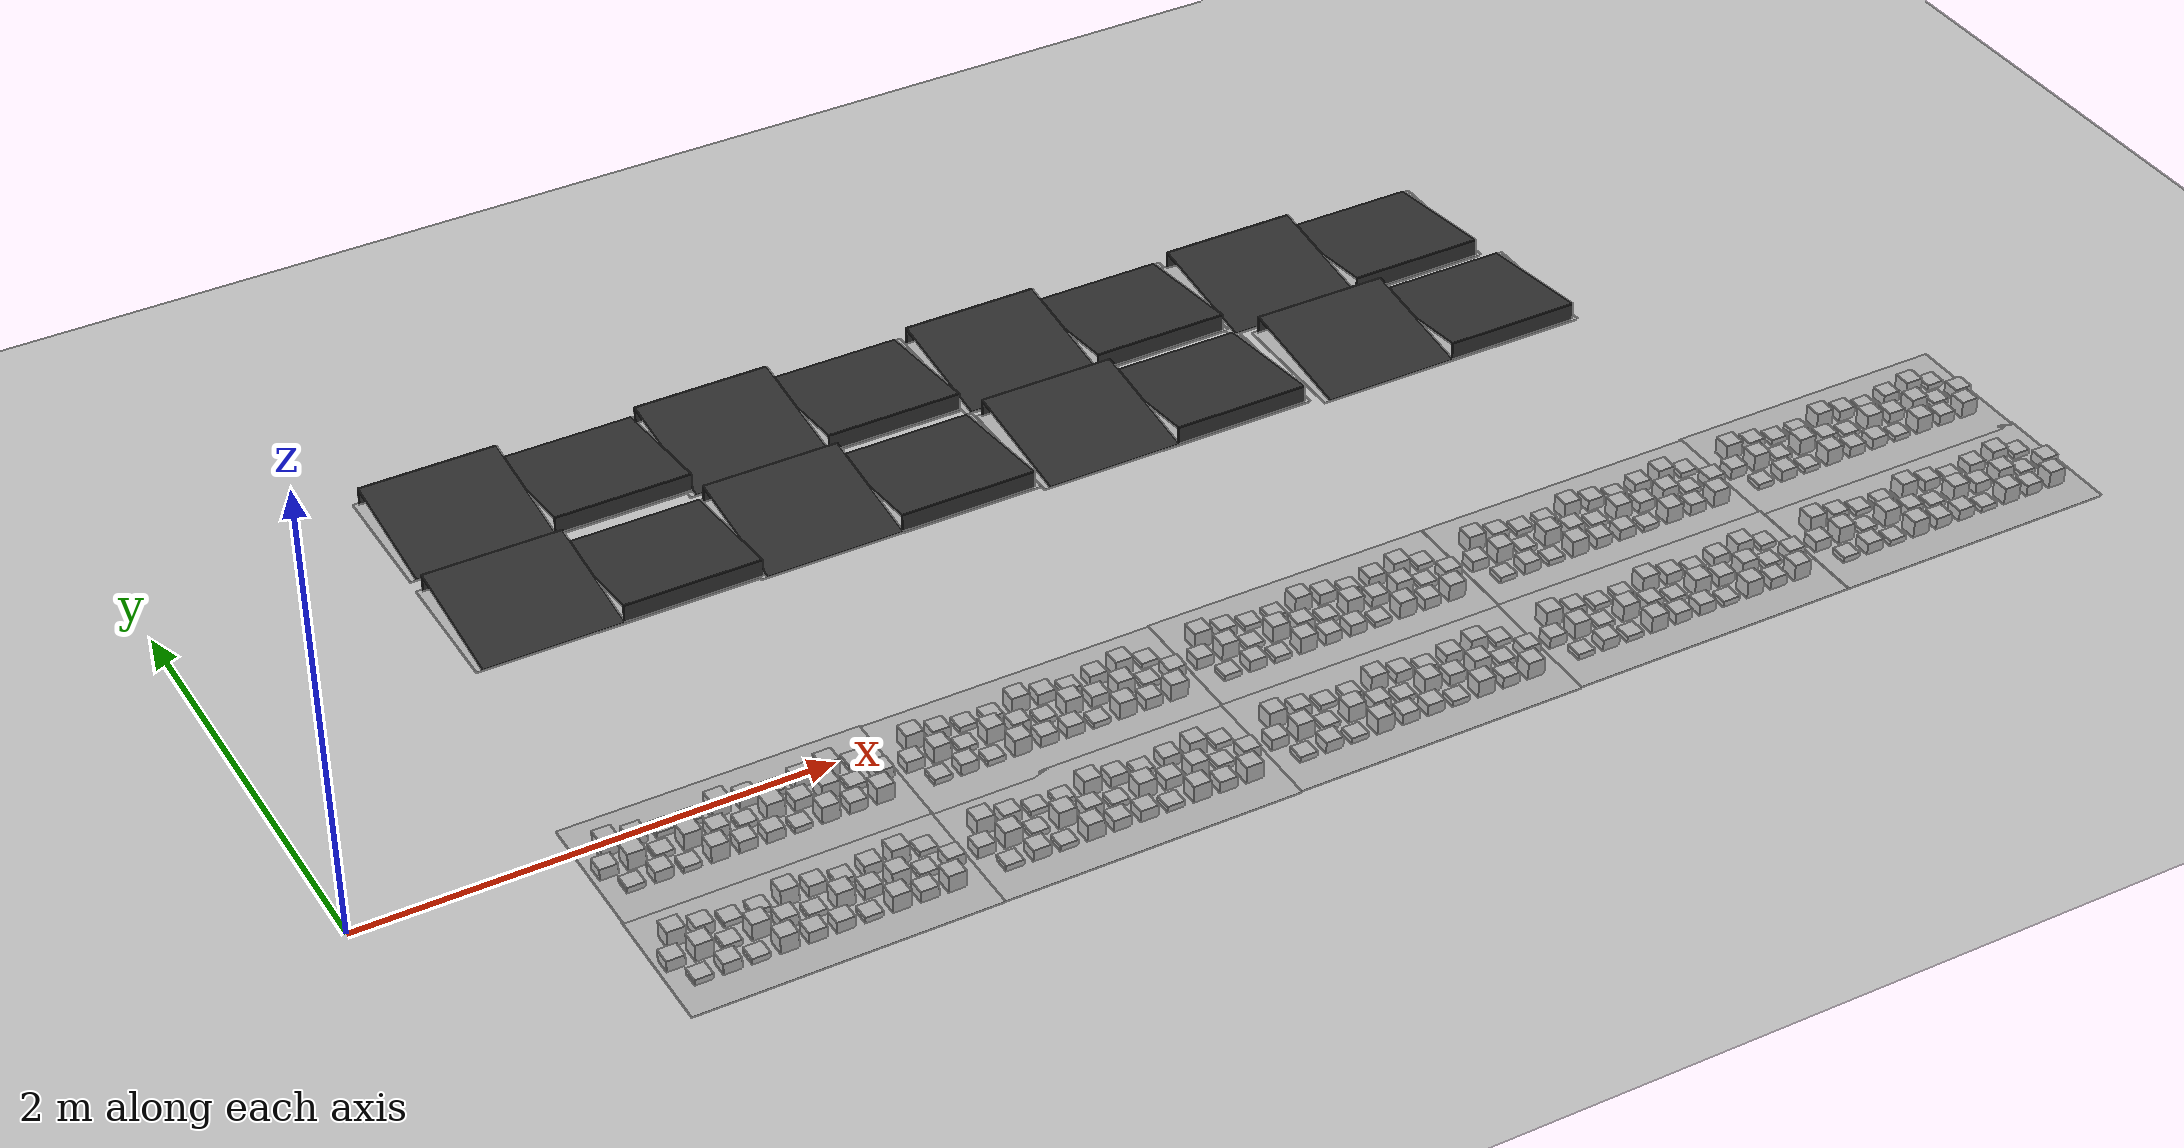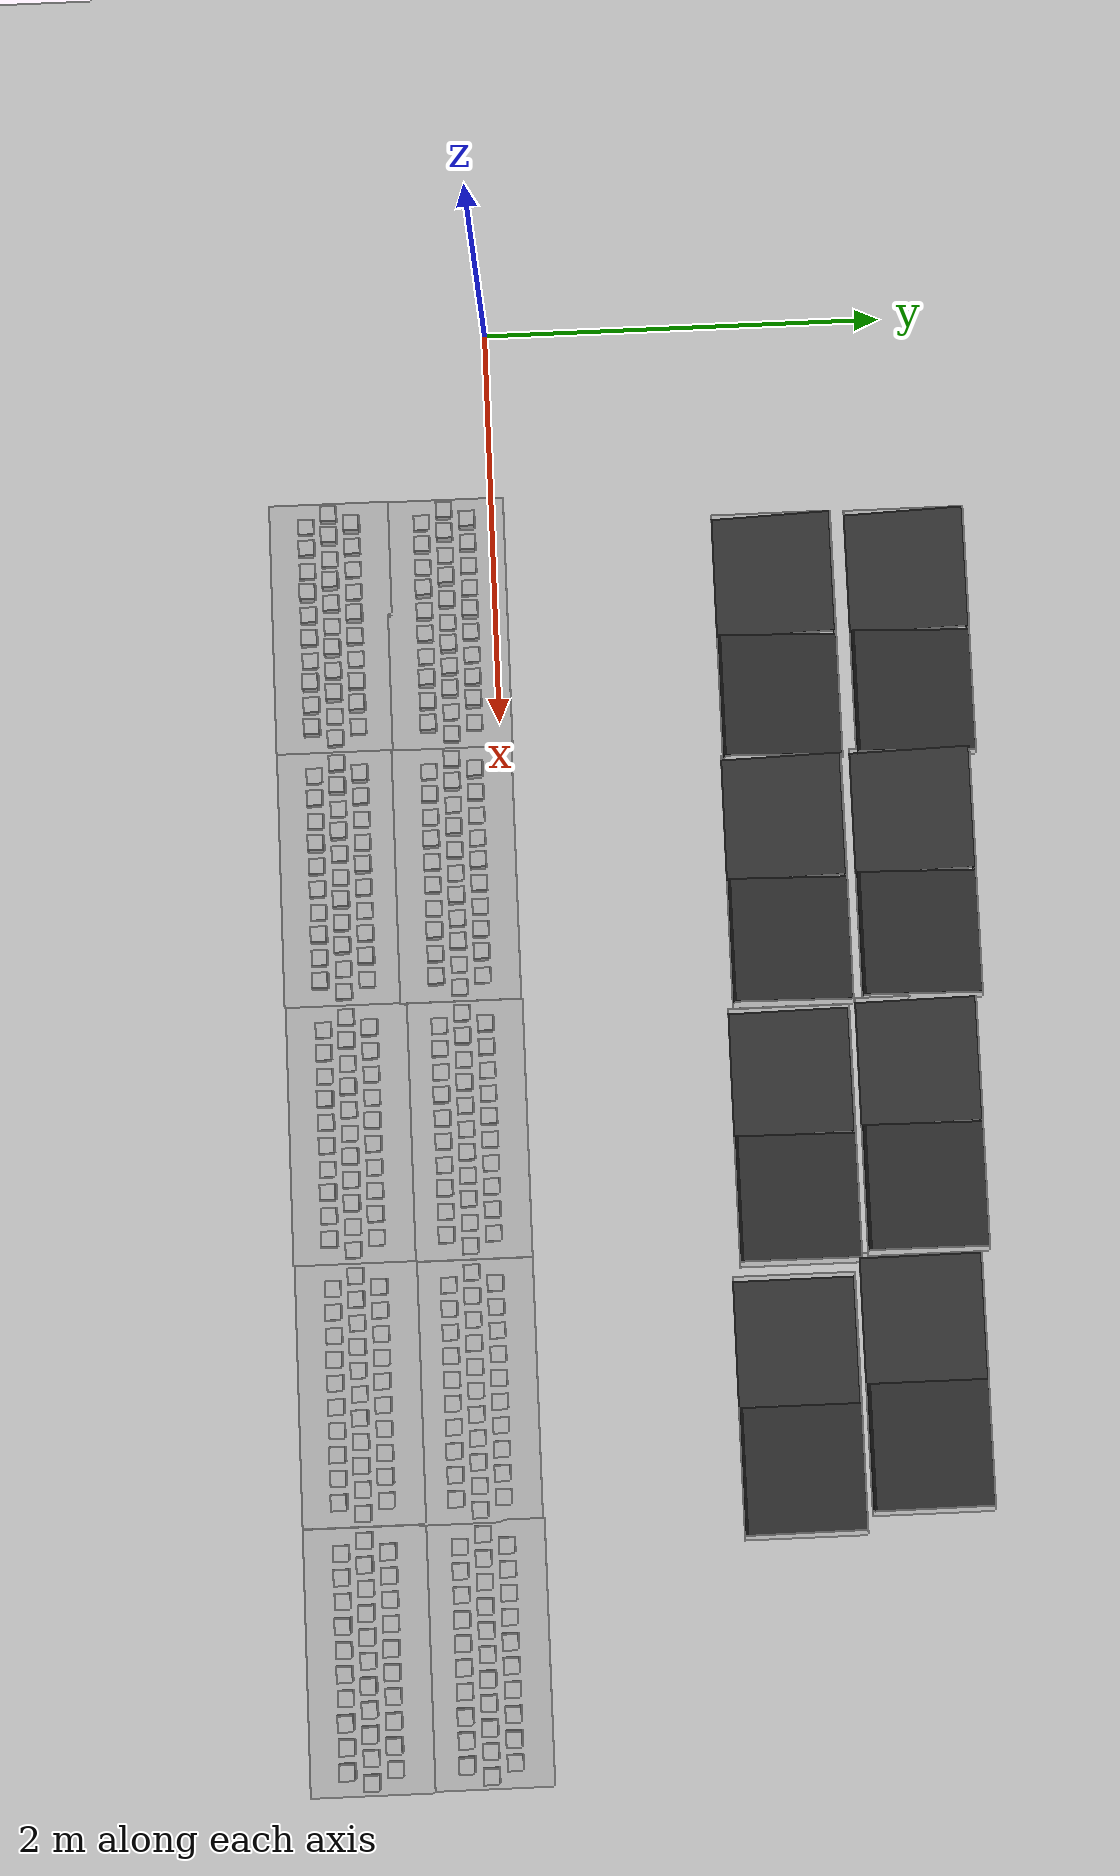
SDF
<sdf version="1.7">
 <world name="default">
  <light name="sun" type="directional">
   <pose>0 0 10 0 -0 0</pose>
   <diffuse>0.8 0.8 0.8 1</diffuse>
   <specular>0.2 0.2 0.2 1</specular>
   <attenuation>
    <range>1000</range>
    <constant>0.9</constant>
    <linear>0.01</linear>
    <quadratic>0.001</quadratic>
   </attenuation>
   <direction>-0.5 0.1 -0.9</direction>
   <spot><inner_angle>0</inner_angle><outer_angle>0</outer_angle><falloff>0</falloff></spot>
  </light>
  <model name="ground_plane">
   <static>1</static>
   <link name="link">
    <collision name="collision">
     <geometry><plane><normal>0 0 1</normal><size>100 100</size></plane></geometry>
     <surface>
      <contact><collide_bitmask>65535</collide_bitmask></contact>
      <friction><ode><mu>100</mu><mu2>50</mu2></ode></friction>
     </surface>
    </collision>
    <visual name="visual">
     <cast_shadows>0</cast_shadows>
     <geometry><plane><normal>0 0 1</normal><size>100 100</size></plane></geometry>
     <material>
      <script><uri>file://media/materials/scripts/gazebo.material</uri><name>Gazebo/Grey</name></script>
     </material>
    </visual>
   </link>
  </model>
  <gravity>0 0 -9.8</gravity>
  <magnetic_field>6e-06 2.3e-05 -4.2e-05</magnetic_field>
  <atmosphere type="adiabatic"/>
  <physics type="ode">
   <max_step_size>0.001</max_step_size>
   <real_time_factor>1</real_time_factor>
   <real_time_update_rate>1000</real_time_update_rate>
  </physics>
  <scene><ambient>0.4 0.4 0.4 1</ambient><background>0.7 0.7 0.7 1</background><shadows>1</shadows></scene>
  <spherical_coordinates>
   <surface_model>EARTH_WGS84</surface_model>
   <latitude_deg>0</latitude_deg>
   <longitude_deg>0</longitude_deg>
   <elevation>0</elevation>
   <heading_deg>0</heading_deg>
  </spherical_coordinates>
  <model name="frc2016_roughterrain">
   <static>1</static>
   <link name="link">
    <visual name="platform">
     <pose>0 0 0.08269 0 -0 0</pose>
     <geometry><box><size>1.27 0.5969 0.003175</size></box></geometry>
    </visual>
    <collision name="platform">
     <pose>0 0 0.08269 0 -0 0</pose>
     <geometry><box><size>1.27 0.5969 0.003175</size></box></geometry>
    </collision>
    <visual name="row1_block1_sm">
     <pose>0.51435 0.1143 0.09698 0 -0 0</pose>
     <geometry><box><size>0.0762 0.0762 0.0254</size></box></geometry>
    </visual>
    <collision name="row1_block1_sm">
     <pose>0.51435 0.1143 0.09698 0 -0 0</pose>
     <geometry><box><size>0.0762 0.0762 0.0254</size></box></geometry>
    </collision>
    <visual name="row1_block2_lg">
     <pose>0.40005 0.1143 0.12238 0 -0 0</pose>
     <geometry><box><size>0.0762 0.0762 0.0762</size></box></geometry>
    </visual>
    <collision name="row1_block2_lg">
     <pose>0.40005 0.1143 0.12238 0 -0 0</pose>
     <geometry><box><size>0.0762 0.0762 0.0762</size></box></geometry>
    </collision>
    <visual name="row1_block3_md">
     <pose>0.28575 0.1143 0.10968 0 -0 0</pose>
     <geometry><box><size>0.0762 0.0762 0.0508</size></box></geometry>
    </visual>
    <collision name="row1_block3_md">
     <pose>0.28575 0.1143 0.10968 0 -0 0</pose>
     <geometry><box><size>0.0762 0.0762 0.0508</size></box></geometry>
    </collision>
    <visual name="row1_block4_sm">
     <pose>0.17145 0.1143 0.09698 0 -0 0</pose>
     <geometry><box><size>0.0762 0.0762 0.0254</size></box></geometry>
    </visual>
    <collision name="row1_block4_sm">
     <pose>0.17145 0.1143 0.09698 0 -0 0</pose>
     <geometry><box><size>0.0762 0.0762 0.0254</size></box></geometry>
    </collision>
    <visual name="row1_block5_md">
     <pose>0.05715 0.1143 0.10968 0 -0 0</pose>
     <geometry><box><size>0.0762 0.0762 0.0508</size></box></geometry>
    </visual>
    <collision name="row1_block5_md">
     <pose>0.05715 0.1143 0.10968 0 -0 0</pose>
     <geometry><box><size>0.0762 0.0762 0.0508</size></box></geometry>
    </collision>
    <visual name="row1_block6_lg">
     <pose>-0.05715 0.1143 0.12238 0 -0 0</pose>
     <geometry><box><size>0.0762 0.0762 0.0762</size></box></geometry>
    </visual>
    <collision name="row1_block6_lg">
     <pose>-0.05715 0.1143 0.12238 0 -0 0</pose>
     <geometry><box><size>0.0762 0.0762 0.0762</size></box></geometry>
    </collision>
    <visual name="row1_block7_sm">
     <pose>-0.17145 0.1143 0.09698 0 -0 0</pose>
     <geometry><box><size>0.0762 0.0762 0.0254</size></box></geometry>
    </visual>
    <collision name="row1_block7_sm">
     <pose>-0.17145 0.1143 0.09698 0 -0 0</pose>
     <geometry><box><size>0.0762 0.0762 0.0254</size></box></geometry>
    </collision>
    <visual name="row1_block8_sm">
     <pose>-0.28575 0.1143 0.09698 0 -0 0</pose>
     <geometry><box><size>0.0762 0.0762 0.0254</size></box></geometry>
    </visual>
    <collision name="row1_block8_sm">
     <pose>-0.28575 0.1143 0.09698 0 -0 0</pose>
     <geometry><box><size>0.0762 0.0762 0.0254</size></box></geometry>
    </collision>
    <visual name="row1_block9_md">
     <pose>-0.40005 0.1143 0.10968 0 -0 0</pose>
     <geometry><box><size>0.0762 0.0762 0.0508</size></box></geometry>
    </visual>
    <collision name="row1_block9_md">
     <pose>-0.40005 0.1143 0.10968 0 -0 0</pose>
     <geometry><box><size>0.0762 0.0762 0.0508</size></box></geometry>
    </collision>
    <visual name="row1_block10_lg">
     <pose>-0.51435 0.1143 0.12238 0 -0 0</pose>
     <geometry><box><size>0.0762 0.0762 0.0762</size></box></geometry>
    </visual>
    <collision name="row1_block10_lg">
     <pose>-0.51435 0.1143 0.12238 0 -0 0</pose>
     <geometry><box><size>0.0762 0.0762 0.0762</size></box></geometry>
    </collision>
    <visual name="row2_block1_md">
     <pose>0.5715 0 0.10968 0 -0 0</pose>
     <geometry><box><size>0.0762 0.0762 0.0508</size></box></geometry>
    </visual>
    <collision name="row2_block1_md">
     <pose>0.5715 0 0.10968 0 -0 0</pose>
     <geometry><box><size>0.0762 0.0762 0.0508</size></box></geometry>
    </collision>
    <visual name="row2_block2_sm">
     <pose>0.4572 0 0.09698 0 -0 0</pose>
     <geometry><box><size>0.0762 0.0762 0.0254</size></box></geometry>
    </visual>
    <collision name="row2_block2_sm">
     <pose>0.4572 0 0.09698 0 -0 0</pose>
     <geometry><box><size>0.0762 0.0762 0.0254</size></box></geometry>
    </collision>
    <visual name="row2_block3_lg">
     <pose>0.3429 0 0.12238 0 -0 0</pose>
     <geometry><box><size>0.0762 0.0762 0.0762</size></box></geometry>
    </visual>
    <collision name="row2_block3_lg">
     <pose>0.3429 0 0.12238 0 -0 0</pose>
     <geometry><box><size>0.0762 0.0762 0.0762</size></box></geometry>
    </collision>
    <visual name="row2_block4_md">
     <pose>0.2286 0 0.10968 0 -0 0</pose>
     <geometry><box><size>0.0762 0.0762 0.0508</size></box></geometry>
    </visual>
    <collision name="row2_block4_md">
     <pose>0.2286 0 0.10968 0 -0 0</pose>
     <geometry><box><size>0.0762 0.0762 0.0508</size></box></geometry>
    </collision>
    <visual name="row2_block5_lg">
     <pose>0.1143 0 0.12238 0 -0 0</pose>
     <geometry><box><size>0.0762 0.0762 0.0762</size></box></geometry>
    </visual>
    <collision name="row2_block5_lg">
     <pose>0.1143 0 0.12238 0 -0 0</pose>
     <geometry><box><size>0.0762 0.0762 0.0762</size></box></geometry>
    </collision>
    <visual name="row2_block6_sm">
     <pose>0 0 0.09698 0 -0 0</pose>
     <geometry><box><size>0.0762 0.0762 0.0254</size></box></geometry>
    </visual>
    <collision name="row2_block6_sm">
     <pose>0 0 0.09698 0 -0 0</pose>
     <geometry><box><size>0.0762 0.0762 0.0254</size></box></geometry>
    </collision>
    <visual name="row2_block7_md">
     <pose>-0.1143 0 0.10968 0 -0 0</pose>
     <geometry><box><size>0.0762 0.0762 0.0508</size></box></geometry>
    </visual>
    <collision name="row2_block7_md">
     <pose>-0.1143 0 0.10968 0 -0 0</pose>
     <geometry><box><size>0.0762 0.0762 0.0508</size></box></geometry>
    </collision>
    <visual name="row2_block8_lg">
     <pose>-0.2286 0 0.12238 0 -0 0</pose>
     <geometry><box><size>0.0762 0.0762 0.0762</size></box></geometry>
    </visual>
    <collision name="row2_block8_lg">
     <pose>-0.2286 0 0.12238 0 -0 0</pose>
     <geometry><box><size>0.0762 0.0762 0.0762</size></box></geometry>
    </collision>
    <visual name="row2_block9_sm">
     <pose>-0.3429 0 0.09698 0 -0 0</pose>
     <geometry><box><size>0.0762 0.0762 0.0254</size></box></geometry>
    </visual>
    <collision name="row2_block9_sm">
     <pose>-0.3429 0 0.09698 0 -0 0</pose>
     <geometry><box><size>0.0762 0.0762 0.0254</size></box></geometry>
    </collision>
    <visual name="row2_block10_lg">
     <pose>-0.4572 0 0.12238 0 -0 0</pose>
     <geometry><box><size>0.0762 0.0762 0.0762</size></box></geometry>
    </visual>
    <collision name="row2_block10_lg">
     <pose>-0.4572 0 0.12238 0 -0 0</pose>
     <geometry><box><size>0.0762 0.0762 0.0762</size></box></geometry>
    </collision>
    <visual name="row2_block11_md">
     <pose>-0.5715 0 0.10968 0 -0 0</pose>
     <geometry><box><size>0.0762 0.0762 0.0508</size></box></geometry>
    </visual>
    <collision name="row2_block11_md">
     <pose>-0.5715 0 0.10968 0 -0 0</pose>
     <geometry><box><size>0.0762 0.0762 0.0508</size></box></geometry>
    </collision>
    <visual name="row3_block1_lg">
     <pose>0.51435 -0.1143 0.12238 0 -0 0</pose>
     <geometry><box><size>0.0762 0.0762 0.0762</size></box></geometry>
    </visual>
    <collision name="row3_block1_lg">
     <pose>0.51435 -0.1143 0.12238 0 -0 0</pose>
     <geometry><box><size>0.0762 0.0762 0.0762</size></box></geometry>
    </collision>
    <visual name="row3_block2_md">
     <pose>0.40005 -0.1143 0.10968 0 -0 0</pose>
     <geometry><box><size>0.0762 0.0762 0.0508</size></box></geometry>
    </visual>
    <collision name="row3_block2_md">
     <pose>0.40005 -0.1143 0.10968 0 -0 0</pose>
     <geometry><box><size>0.0762 0.0762 0.0508</size></box></geometry>
    </collision>
    <visual name="row3_block3_lg">
     <pose>0.28575 -0.1143 0.12238 0 -0 0</pose>
     <geometry><box><size>0.0762 0.0762 0.0762</size></box></geometry>
    </visual>
    <collision name="row3_block3_lg">
     <pose>0.28575 -0.1143 0.12238 0 -0 0</pose>
     <geometry><box><size>0.0762 0.0762 0.0762</size></box></geometry>
    </collision>
    <visual name="row3_block4_sm">
     <pose>0.17145 -0.1143 0.09698 0 -0 0</pose>
     <geometry><box><size>0.0762 0.0762 0.0254</size></box></geometry>
    </visual>
    <collision name="row3_block4_sm">
     <pose>0.17145 -0.1143 0.09698 0 -0 0</pose>
     <geometry><box><size>0.0762 0.0762 0.0254</size></box></geometry>
    </collision>
    <visual name="row3_block5_md">
     <pose>0.05715 -0.1143 0.10968 0 -0 0</pose>
     <geometry><box><size>0.0762 0.0762 0.0508</size></box></geometry>
    </visual>
    <collision name="row3_block5_md">
     <pose>0.05715 -0.1143 0.10968 0 -0 0</pose>
     <geometry><box><size>0.0762 0.0762 0.0508</size></box></geometry>
    </collision>
    <visual name="row3_block6_md">
     <pose>-0.05715 -0.1143 0.10968 0 -0 0</pose>
     <geometry><box><size>0.0762 0.0762 0.0508</size></box></geometry>
    </visual>
    <collision name="row3_block6_md">
     <pose>-0.05715 -0.1143 0.10968 0 -0 0</pose>
     <geometry><box><size>0.0762 0.0762 0.0508</size></box></geometry>
    </collision>
    <visual name="row3_block7_lg">
     <pose>-0.17145 -0.1143 0.12238 0 -0 0</pose>
     <geometry><box><size>0.0762 0.0762 0.0762</size></box></geometry>
    </visual>
    <collision name="row3_block7_lg">
     <pose>-0.17145 -0.1143 0.12238 0 -0 0</pose>
     <geometry><box><size>0.0762 0.0762 0.0762</size></box></geometry>
    </collision>
    <visual name="row3_block8_sm">
     <pose>-0.28575 -0.1143 0.09698 0 -0 0</pose>
     <geometry><box><size>0.0762 0.0762 0.0254</size></box></geometry>
    </visual>
    <collision name="row3_block8_sm">
     <pose>-0.28575 -0.1143 0.09698 0 -0 0</pose>
     <geometry><box><size>0.0762 0.0762 0.0254</size></box></geometry>
    </collision>
    <visual name="row3_block9_md">
     <pose>-0.40005 -0.1143 0.10968 0 -0 0</pose>
     <geometry><box><size>0.0762 0.0762 0.0508</size></box></geometry>
    </visual>
    <collision name="row3_block9_md">
     <pose>-0.40005 -0.1143 0.10968 0 -0 0</pose>
     <geometry><box><size>0.0762 0.0762 0.0508</size></box></geometry>
    </collision>
    <visual name="row3_block10_sm">
     <pose>-0.51435 -0.1143 0.09698 0 -0 0</pose>
     <geometry><box><size>0.0762 0.0762 0.0254</size></box></geometry>
    </visual>
    <collision name="row3_block10_sm">
     <pose>-0.51435 -0.1143 0.09698 0 -0 0</pose>
     <geometry><box><size>0.0762 0.0762 0.0254</size></box></geometry>
    </collision>
   </link>
   <pose>1.50047 -0.238408 0 0 -0 0</pose>
  </model>
  <model name="frc2016_roughterrain_0">
   <static>1</static>
   <link name="link">
    <visual name="platform">
     <pose>0 0 0.08269 0 -0 0</pose>
     <geometry><box><size>1.27 0.5969 0.003175</size></box></geometry>
    </visual>
    <collision name="platform">
     <pose>0 0 0.08269 0 -0 0</pose>
     <geometry><box><size>1.27 0.5969 0.003175</size></box></geometry>
    </collision>
    <visual name="row1_block1_sm">
     <pose>0.51435 0.1143 0.09698 0 -0 0</pose>
     <geometry><box><size>0.0762 0.0762 0.0254</size></box></geometry>
    </visual>
    <collision name="row1_block1_sm">
     <pose>0.51435 0.1143 0.09698 0 -0 0</pose>
     <geometry><box><size>0.0762 0.0762 0.0254</size></box></geometry>
    </collision>
    <visual name="row1_block2_lg">
     <pose>0.40005 0.1143 0.12238 0 -0 0</pose>
     <geometry><box><size>0.0762 0.0762 0.0762</size></box></geometry>
    </visual>
    <collision name="row1_block2_lg">
     <pose>0.40005 0.1143 0.12238 0 -0 0</pose>
     <geometry><box><size>0.0762 0.0762 0.0762</size></box></geometry>
    </collision>
    <visual name="row1_block3_md">
     <pose>0.28575 0.1143 0.10968 0 -0 0</pose>
     <geometry><box><size>0.0762 0.0762 0.0508</size></box></geometry>
    </visual>
    <collision name="row1_block3_md">
     <pose>0.28575 0.1143 0.10968 0 -0 0</pose>
     <geometry><box><size>0.0762 0.0762 0.0508</size></box></geometry>
    </collision>
    <visual name="row1_block4_sm">
     <pose>0.17145 0.1143 0.09698 0 -0 0</pose>
     <geometry><box><size>0.0762 0.0762 0.0254</size></box></geometry>
    </visual>
    <collision name="row1_block4_sm">
     <pose>0.17145 0.1143 0.09698 0 -0 0</pose>
     <geometry><box><size>0.0762 0.0762 0.0254</size></box></geometry>
    </collision>
    <visual name="row1_block5_md">
     <pose>0.05715 0.1143 0.10968 0 -0 0</pose>
     <geometry><box><size>0.0762 0.0762 0.0508</size></box></geometry>
    </visual>
    <collision name="row1_block5_md">
     <pose>0.05715 0.1143 0.10968 0 -0 0</pose>
     <geometry><box><size>0.0762 0.0762 0.0508</size></box></geometry>
    </collision>
    <visual name="row1_block6_lg">
     <pose>-0.05715 0.1143 0.12238 0 -0 0</pose>
     <geometry><box><size>0.0762 0.0762 0.0762</size></box></geometry>
    </visual>
    <collision name="row1_block6_lg">
     <pose>-0.05715 0.1143 0.12238 0 -0 0</pose>
     <geometry><box><size>0.0762 0.0762 0.0762</size></box></geometry>
    </collision>
    <visual name="row1_block7_sm">
     <pose>-0.17145 0.1143 0.09698 0 -0 0</pose>
     <geometry><box><size>0.0762 0.0762 0.0254</size></box></geometry>
    </visual>
    <collision name="row1_block7_sm">
     <pose>-0.17145 0.1143 0.09698 0 -0 0</pose>
     <geometry><box><size>0.0762 0.0762 0.0254</size></box></geometry>
    </collision>
    <visual name="row1_block8_sm">
     <pose>-0.28575 0.1143 0.09698 0 -0 0</pose>
     <geometry><box><size>0.0762 0.0762 0.0254</size></box></geometry>
    </visual>
    <collision name="row1_block8_sm">
     <pose>-0.28575 0.1143 0.09698 0 -0 0</pose>
     <geometry><box><size>0.0762 0.0762 0.0254</size></box></geometry>
    </collision>
    <visual name="row1_block9_md">
     <pose>-0.40005 0.1143 0.10968 0 -0 0</pose>
     <geometry><box><size>0.0762 0.0762 0.0508</size></box></geometry>
    </visual>
    <collision name="row1_block9_md">
     <pose>-0.40005 0.1143 0.10968 0 -0 0</pose>
     <geometry><box><size>0.0762 0.0762 0.0508</size></box></geometry>
    </collision>
    <visual name="row1_block10_lg">
     <pose>-0.51435 0.1143 0.12238 0 -0 0</pose>
     <geometry><box><size>0.0762 0.0762 0.0762</size></box></geometry>
    </visual>
    <collision name="row1_block10_lg">
     <pose>-0.51435 0.1143 0.12238 0 -0 0</pose>
     <geometry><box><size>0.0762 0.0762 0.0762</size></box></geometry>
    </collision>
    <visual name="row2_block1_md">
     <pose>0.5715 0 0.10968 0 -0 0</pose>
     <geometry><box><size>0.0762 0.0762 0.0508</size></box></geometry>
    </visual>
    <collision name="row2_block1_md">
     <pose>0.5715 0 0.10968 0 -0 0</pose>
     <geometry><box><size>0.0762 0.0762 0.0508</size></box></geometry>
    </collision>
    <visual name="row2_block2_sm">
     <pose>0.4572 0 0.09698 0 -0 0</pose>
     <geometry><box><size>0.0762 0.0762 0.0254</size></box></geometry>
    </visual>
    <collision name="row2_block2_sm">
     <pose>0.4572 0 0.09698 0 -0 0</pose>
     <geometry><box><size>0.0762 0.0762 0.0254</size></box></geometry>
    </collision>
    <visual name="row2_block3_lg">
     <pose>0.3429 0 0.12238 0 -0 0</pose>
     <geometry><box><size>0.0762 0.0762 0.0762</size></box></geometry>
    </visual>
    <collision name="row2_block3_lg">
     <pose>0.3429 0 0.12238 0 -0 0</pose>
     <geometry><box><size>0.0762 0.0762 0.0762</size></box></geometry>
    </collision>
    <visual name="row2_block4_md">
     <pose>0.2286 0 0.10968 0 -0 0</pose>
     <geometry><box><size>0.0762 0.0762 0.0508</size></box></geometry>
    </visual>
    <collision name="row2_block4_md">
     <pose>0.2286 0 0.10968 0 -0 0</pose>
     <geometry><box><size>0.0762 0.0762 0.0508</size></box></geometry>
    </collision>
    <visual name="row2_block5_lg">
     <pose>0.1143 0 0.12238 0 -0 0</pose>
     <geometry><box><size>0.0762 0.0762 0.0762</size></box></geometry>
    </visual>
    <collision name="row2_block5_lg">
     <pose>0.1143 0 0.12238 0 -0 0</pose>
     <geometry><box><size>0.0762 0.0762 0.0762</size></box></geometry>
    </collision>
    <visual name="row2_block6_sm">
     <pose>0 0 0.09698 0 -0 0</pose>
     <geometry><box><size>0.0762 0.0762 0.0254</size></box></geometry>
    </visual>
    <collision name="row2_block6_sm">
     <pose>0 0 0.09698 0 -0 0</pose>
     <geometry><box><size>0.0762 0.0762 0.0254</size></box></geometry>
    </collision>
    <visual name="row2_block7_md">
     <pose>-0.1143 0 0.10968 0 -0 0</pose>
     <geometry><box><size>0.0762 0.0762 0.0508</size></box></geometry>
    </visual>
    <collision name="row2_block7_md">
     <pose>-0.1143 0 0.10968 0 -0 0</pose>
     <geometry><box><size>0.0762 0.0762 0.0508</size></box></geometry>
    </collision>
    <visual name="row2_block8_lg">
     <pose>-0.2286 0 0.12238 0 -0 0</pose>
     <geometry><box><size>0.0762 0.0762 0.0762</size></box></geometry>
    </visual>
    <collision name="row2_block8_lg">
     <pose>-0.2286 0 0.12238 0 -0 0</pose>
     <geometry><box><size>0.0762 0.0762 0.0762</size></box></geometry>
    </collision>
    <visual name="row2_block9_sm">
     <pose>-0.3429 0 0.09698 0 -0 0</pose>
     <geometry><box><size>0.0762 0.0762 0.0254</size></box></geometry>
    </visual>
    <collision name="row2_block9_sm">
     <pose>-0.3429 0 0.09698 0 -0 0</pose>
     <geometry><box><size>0.0762 0.0762 0.0254</size></box></geometry>
    </collision>
    <visual name="row2_block10_lg">
     <pose>-0.4572 0 0.12238 0 -0 0</pose>
     <geometry><box><size>0.0762 0.0762 0.0762</size></box></geometry>
    </visual>
    <collision name="row2_block10_lg">
     <pose>-0.4572 0 0.12238 0 -0 0</pose>
     <geometry><box><size>0.0762 0.0762 0.0762</size></box></geometry>
    </collision>
    <visual name="row2_block11_md">
     <pose>-0.5715 0 0.10968 0 -0 0</pose>
     <geometry><box><size>0.0762 0.0762 0.0508</size></box></geometry>
    </visual>
    <collision name="row2_block11_md">
     <pose>-0.5715 0 0.10968 0 -0 0</pose>
     <geometry><box><size>0.0762 0.0762 0.0508</size></box></geometry>
    </collision>
    <visual name="row3_block1_lg">
     <pose>0.51435 -0.1143 0.12238 0 -0 0</pose>
     <geometry><box><size>0.0762 0.0762 0.0762</size></box></geometry>
    </visual>
    <collision name="row3_block1_lg">
     <pose>0.51435 -0.1143 0.12238 0 -0 0</pose>
     <geometry><box><size>0.0762 0.0762 0.0762</size></box></geometry>
    </collision>
    <visual name="row3_block2_md">
     <pose>0.40005 -0.1143 0.10968 0 -0 0</pose>
     <geometry><box><size>0.0762 0.0762 0.0508</size></box></geometry>
    </visual>
    <collision name="row3_block2_md">
     <pose>0.40005 -0.1143 0.10968 0 -0 0</pose>
     <geometry><box><size>0.0762 0.0762 0.0508</size></box></geometry>
    </collision>
    <visual name="row3_block3_lg">
     <pose>0.28575 -0.1143 0.12238 0 -0 0</pose>
     <geometry><box><size>0.0762 0.0762 0.0762</size></box></geometry>
    </visual>
    <collision name="row3_block3_lg">
     <pose>0.28575 -0.1143 0.12238 0 -0 0</pose>
     <geometry><box><size>0.0762 0.0762 0.0762</size></box></geometry>
    </collision>
    <visual name="row3_block4_sm">
     <pose>0.17145 -0.1143 0.09698 0 -0 0</pose>
     <geometry><box><size>0.0762 0.0762 0.0254</size></box></geometry>
    </visual>
    <collision name="row3_block4_sm">
     <pose>0.17145 -0.1143 0.09698 0 -0 0</pose>
     <geometry><box><size>0.0762 0.0762 0.0254</size></box></geometry>
    </collision>
    <visual name="row3_block5_md">
     <pose>0.05715 -0.1143 0.10968 0 -0 0</pose>
     <geometry><box><size>0.0762 0.0762 0.0508</size></box></geometry>
    </visual>
    <collision name="row3_block5_md">
     <pose>0.05715 -0.1143 0.10968 0 -0 0</pose>
     <geometry><box><size>0.0762 0.0762 0.0508</size></box></geometry>
    </collision>
    <visual name="row3_block6_md">
     <pose>-0.05715 -0.1143 0.10968 0 -0 0</pose>
     <geometry><box><size>0.0762 0.0762 0.0508</size></box></geometry>
    </visual>
    <collision name="row3_block6_md">
     <pose>-0.05715 -0.1143 0.10968 0 -0 0</pose>
     <geometry><box><size>0.0762 0.0762 0.0508</size></box></geometry>
    </collision>
    <visual name="row3_block7_lg">
     <pose>-0.17145 -0.1143 0.12238 0 -0 0</pose>
     <geometry><box><size>0.0762 0.0762 0.0762</size></box></geometry>
    </visual>
    <collision name="row3_block7_lg">
     <pose>-0.17145 -0.1143 0.12238 0 -0 0</pose>
     <geometry><box><size>0.0762 0.0762 0.0762</size></box></geometry>
    </collision>
    <visual name="row3_block8_sm">
     <pose>-0.28575 -0.1143 0.09698 0 -0 0</pose>
     <geometry><box><size>0.0762 0.0762 0.0254</size></box></geometry>
    </visual>
    <collision name="row3_block8_sm">
     <pose>-0.28575 -0.1143 0.09698 0 -0 0</pose>
     <geometry><box><size>0.0762 0.0762 0.0254</size></box></geometry>
    </collision>
    <visual name="row3_block9_md">
     <pose>-0.40005 -0.1143 0.10968 0 -0 0</pose>
     <geometry><box><size>0.0762 0.0762 0.0508</size></box></geometry>
    </visual>
    <collision name="row3_block9_md">
     <pose>-0.40005 -0.1143 0.10968 0 -0 0</pose>
     <geometry><box><size>0.0762 0.0762 0.0508</size></box></geometry>
    </collision>
    <visual name="row3_block10_sm">
     <pose>-0.51435 -0.1143 0.09698 0 -0 0</pose>
     <geometry><box><size>0.0762 0.0762 0.0254</size></box></geometry>
    </visual>
    <collision name="row3_block10_sm">
     <pose>-0.51435 -0.1143 0.09698 0 -0 0</pose>
     <geometry><box><size>0.0762 0.0762 0.0254</size></box></geometry>
    </collision>
   </link>
   <pose>1.49738 -0.816433 0 0 -0 0</pose>
  </model>
  <model name="frc2016_roughterrain_1">
   <static>1</static>
   <link name="link">
    <visual name="platform">
     <pose>0 0 0.08269 0 -0 0</pose>
     <geometry><box><size>1.27 0.5969 0.003175</size></box></geometry>
    </visual>
    <collision name="platform">
     <pose>0 0 0.08269 0 -0 0</pose>
     <geometry><box><size>1.27 0.5969 0.003175</size></box></geometry>
    </collision>
    <visual name="row1_block1_sm">
     <pose>0.51435 0.1143 0.09698 0 -0 0</pose>
     <geometry><box><size>0.0762 0.0762 0.0254</size></box></geometry>
    </visual>
    <collision name="row1_block1_sm">
     <pose>0.51435 0.1143 0.09698 0 -0 0</pose>
     <geometry><box><size>0.0762 0.0762 0.0254</size></box></geometry>
    </collision>
    <visual name="row1_block2_lg">
     <pose>0.40005 0.1143 0.12238 0 -0 0</pose>
     <geometry><box><size>0.0762 0.0762 0.0762</size></box></geometry>
    </visual>
    <collision name="row1_block2_lg">
     <pose>0.40005 0.1143 0.12238 0 -0 0</pose>
     <geometry><box><size>0.0762 0.0762 0.0762</size></box></geometry>
    </collision>
    <visual name="row1_block3_md">
     <pose>0.28575 0.1143 0.10968 0 -0 0</pose>
     <geometry><box><size>0.0762 0.0762 0.0508</size></box></geometry>
    </visual>
    <collision name="row1_block3_md">
     <pose>0.28575 0.1143 0.10968 0 -0 0</pose>
     <geometry><box><size>0.0762 0.0762 0.0508</size></box></geometry>
    </collision>
    <visual name="row1_block4_sm">
     <pose>0.17145 0.1143 0.09698 0 -0 0</pose>
     <geometry><box><size>0.0762 0.0762 0.0254</size></box></geometry>
    </visual>
    <collision name="row1_block4_sm">
     <pose>0.17145 0.1143 0.09698 0 -0 0</pose>
     <geometry><box><size>0.0762 0.0762 0.0254</size></box></geometry>
    </collision>
    <visual name="row1_block5_md">
     <pose>0.05715 0.1143 0.10968 0 -0 0</pose>
     <geometry><box><size>0.0762 0.0762 0.0508</size></box></geometry>
    </visual>
    <collision name="row1_block5_md">
     <pose>0.05715 0.1143 0.10968 0 -0 0</pose>
     <geometry><box><size>0.0762 0.0762 0.0508</size></box></geometry>
    </collision>
    <visual name="row1_block6_lg">
     <pose>-0.05715 0.1143 0.12238 0 -0 0</pose>
     <geometry><box><size>0.0762 0.0762 0.0762</size></box></geometry>
    </visual>
    <collision name="row1_block6_lg">
     <pose>-0.05715 0.1143 0.12238 0 -0 0</pose>
     <geometry><box><size>0.0762 0.0762 0.0762</size></box></geometry>
    </collision>
    <visual name="row1_block7_sm">
     <pose>-0.17145 0.1143 0.09698 0 -0 0</pose>
     <geometry><box><size>0.0762 0.0762 0.0254</size></box></geometry>
    </visual>
    <collision name="row1_block7_sm">
     <pose>-0.17145 0.1143 0.09698 0 -0 0</pose>
     <geometry><box><size>0.0762 0.0762 0.0254</size></box></geometry>
    </collision>
    <visual name="row1_block8_sm">
     <pose>-0.28575 0.1143 0.09698 0 -0 0</pose>
     <geometry><box><size>0.0762 0.0762 0.0254</size></box></geometry>
    </visual>
    <collision name="row1_block8_sm">
     <pose>-0.28575 0.1143 0.09698 0 -0 0</pose>
     <geometry><box><size>0.0762 0.0762 0.0254</size></box></geometry>
    </collision>
    <visual name="row1_block9_md">
     <pose>-0.40005 0.1143 0.10968 0 -0 0</pose>
     <geometry><box><size>0.0762 0.0762 0.0508</size></box></geometry>
    </visual>
    <collision name="row1_block9_md">
     <pose>-0.40005 0.1143 0.10968 0 -0 0</pose>
     <geometry><box><size>0.0762 0.0762 0.0508</size></box></geometry>
    </collision>
    <visual name="row1_block10_lg">
     <pose>-0.51435 0.1143 0.12238 0 -0 0</pose>
     <geometry><box><size>0.0762 0.0762 0.0762</size></box></geometry>
    </visual>
    <collision name="row1_block10_lg">
     <pose>-0.51435 0.1143 0.12238 0 -0 0</pose>
     <geometry><box><size>0.0762 0.0762 0.0762</size></box></geometry>
    </collision>
    <visual name="row2_block1_md">
     <pose>0.5715 0 0.10968 0 -0 0</pose>
     <geometry><box><size>0.0762 0.0762 0.0508</size></box></geometry>
    </visual>
    <collision name="row2_block1_md">
     <pose>0.5715 0 0.10968 0 -0 0</pose>
     <geometry><box><size>0.0762 0.0762 0.0508</size></box></geometry>
    </collision>
    <visual name="row2_block2_sm">
     <pose>0.4572 0 0.09698 0 -0 0</pose>
     <geometry><box><size>0.0762 0.0762 0.0254</size></box></geometry>
    </visual>
    <collision name="row2_block2_sm">
     <pose>0.4572 0 0.09698 0 -0 0</pose>
     <geometry><box><size>0.0762 0.0762 0.0254</size></box></geometry>
    </collision>
    <visual name="row2_block3_lg">
     <pose>0.3429 0 0.12238 0 -0 0</pose>
     <geometry><box><size>0.0762 0.0762 0.0762</size></box></geometry>
    </visual>
    <collision name="row2_block3_lg">
     <pose>0.3429 0 0.12238 0 -0 0</pose>
     <geometry><box><size>0.0762 0.0762 0.0762</size></box></geometry>
    </collision>
    <visual name="row2_block4_md">
     <pose>0.2286 0 0.10968 0 -0 0</pose>
     <geometry><box><size>0.0762 0.0762 0.0508</size></box></geometry>
    </visual>
    <collision name="row2_block4_md">
     <pose>0.2286 0 0.10968 0 -0 0</pose>
     <geometry><box><size>0.0762 0.0762 0.0508</size></box></geometry>
    </collision>
    <visual name="row2_block5_lg">
     <pose>0.1143 0 0.12238 0 -0 0</pose>
     <geometry><box><size>0.0762 0.0762 0.0762</size></box></geometry>
    </visual>
    <collision name="row2_block5_lg">
     <pose>0.1143 0 0.12238 0 -0 0</pose>
     <geometry><box><size>0.0762 0.0762 0.0762</size></box></geometry>
    </collision>
    <visual name="row2_block6_sm">
     <pose>0 0 0.09698 0 -0 0</pose>
     <geometry><box><size>0.0762 0.0762 0.0254</size></box></geometry>
    </visual>
    <collision name="row2_block6_sm">
     <pose>0 0 0.09698 0 -0 0</pose>
     <geometry><box><size>0.0762 0.0762 0.0254</size></box></geometry>
    </collision>
    <visual name="row2_block7_md">
     <pose>-0.1143 0 0.10968 0 -0 0</pose>
     <geometry><box><size>0.0762 0.0762 0.0508</size></box></geometry>
    </visual>
    <collision name="row2_block7_md">
     <pose>-0.1143 0 0.10968 0 -0 0</pose>
     <geometry><box><size>0.0762 0.0762 0.0508</size></box></geometry>
    </collision>
    <visual name="row2_block8_lg">
     <pose>-0.2286 0 0.12238 0 -0 0</pose>
     <geometry><box><size>0.0762 0.0762 0.0762</size></box></geometry>
    </visual>
    <collision name="row2_block8_lg">
     <pose>-0.2286 0 0.12238 0 -0 0</pose>
     <geometry><box><size>0.0762 0.0762 0.0762</size></box></geometry>
    </collision>
    <visual name="row2_block9_sm">
     <pose>-0.3429 0 0.09698 0 -0 0</pose>
     <geometry><box><size>0.0762 0.0762 0.0254</size></box></geometry>
    </visual>
    <collision name="row2_block9_sm">
     <pose>-0.3429 0 0.09698 0 -0 0</pose>
     <geometry><box><size>0.0762 0.0762 0.0254</size></box></geometry>
    </collision>
    <visual name="row2_block10_lg">
     <pose>-0.4572 0 0.12238 0 -0 0</pose>
     <geometry><box><size>0.0762 0.0762 0.0762</size></box></geometry>
    </visual>
    <collision name="row2_block10_lg">
     <pose>-0.4572 0 0.12238 0 -0 0</pose>
     <geometry><box><size>0.0762 0.0762 0.0762</size></box></geometry>
    </collision>
    <visual name="row2_block11_md">
     <pose>-0.5715 0 0.10968 0 -0 0</pose>
     <geometry><box><size>0.0762 0.0762 0.0508</size></box></geometry>
    </visual>
    <collision name="row2_block11_md">
     <pose>-0.5715 0 0.10968 0 -0 0</pose>
     <geometry><box><size>0.0762 0.0762 0.0508</size></box></geometry>
    </collision>
    <visual name="row3_block1_lg">
     <pose>0.51435 -0.1143 0.12238 0 -0 0</pose>
     <geometry><box><size>0.0762 0.0762 0.0762</size></box></geometry>
    </visual>
    <collision name="row3_block1_lg">
     <pose>0.51435 -0.1143 0.12238 0 -0 0</pose>
     <geometry><box><size>0.0762 0.0762 0.0762</size></box></geometry>
    </collision>
    <visual name="row3_block2_md">
     <pose>0.40005 -0.1143 0.10968 0 -0 0</pose>
     <geometry><box><size>0.0762 0.0762 0.0508</size></box></geometry>
    </visual>
    <collision name="row3_block2_md">
     <pose>0.40005 -0.1143 0.10968 0 -0 0</pose>
     <geometry><box><size>0.0762 0.0762 0.0508</size></box></geometry>
    </collision>
    <visual name="row3_block3_lg">
     <pose>0.28575 -0.1143 0.12238 0 -0 0</pose>
     <geometry><box><size>0.0762 0.0762 0.0762</size></box></geometry>
    </visual>
    <collision name="row3_block3_lg">
     <pose>0.28575 -0.1143 0.12238 0 -0 0</pose>
     <geometry><box><size>0.0762 0.0762 0.0762</size></box></geometry>
    </collision>
    <visual name="row3_block4_sm">
     <pose>0.17145 -0.1143 0.09698 0 -0 0</pose>
     <geometry><box><size>0.0762 0.0762 0.0254</size></box></geometry>
    </visual>
    <collision name="row3_block4_sm">
     <pose>0.17145 -0.1143 0.09698 0 -0 0</pose>
     <geometry><box><size>0.0762 0.0762 0.0254</size></box></geometry>
    </collision>
    <visual name="row3_block5_md">
     <pose>0.05715 -0.1143 0.10968 0 -0 0</pose>
     <geometry><box><size>0.0762 0.0762 0.0508</size></box></geometry>
    </visual>
    <collision name="row3_block5_md">
     <pose>0.05715 -0.1143 0.10968 0 -0 0</pose>
     <geometry><box><size>0.0762 0.0762 0.0508</size></box></geometry>
    </collision>
    <visual name="row3_block6_md">
     <pose>-0.05715 -0.1143 0.10968 0 -0 0</pose>
     <geometry><box><size>0.0762 0.0762 0.0508</size></box></geometry>
    </visual>
    <collision name="row3_block6_md">
     <pose>-0.05715 -0.1143 0.10968 0 -0 0</pose>
     <geometry><box><size>0.0762 0.0762 0.0508</size></box></geometry>
    </collision>
    <visual name="row3_block7_lg">
     <pose>-0.17145 -0.1143 0.12238 0 -0 0</pose>
     <geometry><box><size>0.0762 0.0762 0.0762</size></box></geometry>
    </visual>
    <collision name="row3_block7_lg">
     <pose>-0.17145 -0.1143 0.12238 0 -0 0</pose>
     <geometry><box><size>0.0762 0.0762 0.0762</size></box></geometry>
    </collision>
    <visual name="row3_block8_sm">
     <pose>-0.28575 -0.1143 0.09698 0 -0 0</pose>
     <geometry><box><size>0.0762 0.0762 0.0254</size></box></geometry>
    </visual>
    <collision name="row3_block8_sm">
     <pose>-0.28575 -0.1143 0.09698 0 -0 0</pose>
     <geometry><box><size>0.0762 0.0762 0.0254</size></box></geometry>
    </collision>
    <visual name="row3_block9_md">
     <pose>-0.40005 -0.1143 0.10968 0 -0 0</pose>
     <geometry><box><size>0.0762 0.0762 0.0508</size></box></geometry>
    </visual>
    <collision name="row3_block9_md">
     <pose>-0.40005 -0.1143 0.10968 0 -0 0</pose>
     <geometry><box><size>0.0762 0.0762 0.0508</size></box></geometry>
    </collision>
    <visual name="row3_block10_sm">
     <pose>-0.51435 -0.1143 0.09698 0 -0 0</pose>
     <geometry><box><size>0.0762 0.0762 0.0254</size></box></geometry>
    </visual>
    <collision name="row3_block10_sm">
     <pose>-0.51435 -0.1143 0.09698 0 -0 0</pose>
     <geometry><box><size>0.0762 0.0762 0.0254</size></box></geometry>
    </collision>
   </link>
   <pose>2.76949 -0.245026 0 0 -0 0</pose>
  </model>
  <model name="frc2016_roughterrain_2">
   <static>1</static>
   <link name="link">
    <visual name="platform">
     <pose>0 0 0.08269 0 -0 0</pose>
     <geometry><box><size>1.27 0.5969 0.003175</size></box></geometry>
    </visual>
    <collision name="platform">
     <pose>0 0 0.08269 0 -0 0</pose>
     <geometry><box><size>1.27 0.5969 0.003175</size></box></geometry>
    </collision>
    <visual name="row1_block1_sm">
     <pose>0.51435 0.1143 0.09698 0 -0 0</pose>
     <geometry><box><size>0.0762 0.0762 0.0254</size></box></geometry>
    </visual>
    <collision name="row1_block1_sm">
     <pose>0.51435 0.1143 0.09698 0 -0 0</pose>
     <geometry><box><size>0.0762 0.0762 0.0254</size></box></geometry>
    </collision>
    <visual name="row1_block2_lg">
     <pose>0.40005 0.1143 0.12238 0 -0 0</pose>
     <geometry><box><size>0.0762 0.0762 0.0762</size></box></geometry>
    </visual>
    <collision name="row1_block2_lg">
     <pose>0.40005 0.1143 0.12238 0 -0 0</pose>
     <geometry><box><size>0.0762 0.0762 0.0762</size></box></geometry>
    </collision>
    <visual name="row1_block3_md">
     <pose>0.28575 0.1143 0.10968 0 -0 0</pose>
     <geometry><box><size>0.0762 0.0762 0.0508</size></box></geometry>
    </visual>
    <collision name="row1_block3_md">
     <pose>0.28575 0.1143 0.10968 0 -0 0</pose>
     <geometry><box><size>0.0762 0.0762 0.0508</size></box></geometry>
    </collision>
    <visual name="row1_block4_sm">
     <pose>0.17145 0.1143 0.09698 0 -0 0</pose>
     <geometry><box><size>0.0762 0.0762 0.0254</size></box></geometry>
    </visual>
    <collision name="row1_block4_sm">
     <pose>0.17145 0.1143 0.09698 0 -0 0</pose>
     <geometry><box><size>0.0762 0.0762 0.0254</size></box></geometry>
    </collision>
    <visual name="row1_block5_md">
     <pose>0.05715 0.1143 0.10968 0 -0 0</pose>
     <geometry><box><size>0.0762 0.0762 0.0508</size></box></geometry>
    </visual>
    <collision name="row1_block5_md">
     <pose>0.05715 0.1143 0.10968 0 -0 0</pose>
     <geometry><box><size>0.0762 0.0762 0.0508</size></box></geometry>
    </collision>
    <visual name="row1_block6_lg">
     <pose>-0.05715 0.1143 0.12238 0 -0 0</pose>
     <geometry><box><size>0.0762 0.0762 0.0762</size></box></geometry>
    </visual>
    <collision name="row1_block6_lg">
     <pose>-0.05715 0.1143 0.12238 0 -0 0</pose>
     <geometry><box><size>0.0762 0.0762 0.0762</size></box></geometry>
    </collision>
    <visual name="row1_block7_sm">
     <pose>-0.17145 0.1143 0.09698 0 -0 0</pose>
     <geometry><box><size>0.0762 0.0762 0.0254</size></box></geometry>
    </visual>
    <collision name="row1_block7_sm">
     <pose>-0.17145 0.1143 0.09698 0 -0 0</pose>
     <geometry><box><size>0.0762 0.0762 0.0254</size></box></geometry>
    </collision>
    <visual name="row1_block8_sm">
     <pose>-0.28575 0.1143 0.09698 0 -0 0</pose>
     <geometry><box><size>0.0762 0.0762 0.0254</size></box></geometry>
    </visual>
    <collision name="row1_block8_sm">
     <pose>-0.28575 0.1143 0.09698 0 -0 0</pose>
     <geometry><box><size>0.0762 0.0762 0.0254</size></box></geometry>
    </collision>
    <visual name="row1_block9_md">
     <pose>-0.40005 0.1143 0.10968 0 -0 0</pose>
     <geometry><box><size>0.0762 0.0762 0.0508</size></box></geometry>
    </visual>
    <collision name="row1_block9_md">
     <pose>-0.40005 0.1143 0.10968 0 -0 0</pose>
     <geometry><box><size>0.0762 0.0762 0.0508</size></box></geometry>
    </collision>
    <visual name="row1_block10_lg">
     <pose>-0.51435 0.1143 0.12238 0 -0 0</pose>
     <geometry><box><size>0.0762 0.0762 0.0762</size></box></geometry>
    </visual>
    <collision name="row1_block10_lg">
     <pose>-0.51435 0.1143 0.12238 0 -0 0</pose>
     <geometry><box><size>0.0762 0.0762 0.0762</size></box></geometry>
    </collision>
    <visual name="row2_block1_md">
     <pose>0.5715 0 0.10968 0 -0 0</pose>
     <geometry><box><size>0.0762 0.0762 0.0508</size></box></geometry>
    </visual>
    <collision name="row2_block1_md">
     <pose>0.5715 0 0.10968 0 -0 0</pose>
     <geometry><box><size>0.0762 0.0762 0.0508</size></box></geometry>
    </collision>
    <visual name="row2_block2_sm">
     <pose>0.4572 0 0.09698 0 -0 0</pose>
     <geometry><box><size>0.0762 0.0762 0.0254</size></box></geometry>
    </visual>
    <collision name="row2_block2_sm">
     <pose>0.4572 0 0.09698 0 -0 0</pose>
     <geometry><box><size>0.0762 0.0762 0.0254</size></box></geometry>
    </collision>
    <visual name="row2_block3_lg">
     <pose>0.3429 0 0.12238 0 -0 0</pose>
     <geometry><box><size>0.0762 0.0762 0.0762</size></box></geometry>
    </visual>
    <collision name="row2_block3_lg">
     <pose>0.3429 0 0.12238 0 -0 0</pose>
     <geometry><box><size>0.0762 0.0762 0.0762</size></box></geometry>
    </collision>
    <visual name="row2_block4_md">
     <pose>0.2286 0 0.10968 0 -0 0</pose>
     <geometry><box><size>0.0762 0.0762 0.0508</size></box></geometry>
    </visual>
    <collision name="row2_block4_md">
     <pose>0.2286 0 0.10968 0 -0 0</pose>
     <geometry><box><size>0.0762 0.0762 0.0508</size></box></geometry>
    </collision>
    <visual name="row2_block5_lg">
     <pose>0.1143 0 0.12238 0 -0 0</pose>
     <geometry><box><size>0.0762 0.0762 0.0762</size></box></geometry>
    </visual>
    <collision name="row2_block5_lg">
     <pose>0.1143 0 0.12238 0 -0 0</pose>
     <geometry><box><size>0.0762 0.0762 0.0762</size></box></geometry>
    </collision>
    <visual name="row2_block6_sm">
     <pose>0 0 0.09698 0 -0 0</pose>
     <geometry><box><size>0.0762 0.0762 0.0254</size></box></geometry>
    </visual>
    <collision name="row2_block6_sm">
     <pose>0 0 0.09698 0 -0 0</pose>
     <geometry><box><size>0.0762 0.0762 0.0254</size></box></geometry>
    </collision>
    <visual name="row2_block7_md">
     <pose>-0.1143 0 0.10968 0 -0 0</pose>
     <geometry><box><size>0.0762 0.0762 0.0508</size></box></geometry>
    </visual>
    <collision name="row2_block7_md">
     <pose>-0.1143 0 0.10968 0 -0 0</pose>
     <geometry><box><size>0.0762 0.0762 0.0508</size></box></geometry>
    </collision>
    <visual name="row2_block8_lg">
     <pose>-0.2286 0 0.12238 0 -0 0</pose>
     <geometry><box><size>0.0762 0.0762 0.0762</size></box></geometry>
    </visual>
    <collision name="row2_block8_lg">
     <pose>-0.2286 0 0.12238 0 -0 0</pose>
     <geometry><box><size>0.0762 0.0762 0.0762</size></box></geometry>
    </collision>
    <visual name="row2_block9_sm">
     <pose>-0.3429 0 0.09698 0 -0 0</pose>
     <geometry><box><size>0.0762 0.0762 0.0254</size></box></geometry>
    </visual>
    <collision name="row2_block9_sm">
     <pose>-0.3429 0 0.09698 0 -0 0</pose>
     <geometry><box><size>0.0762 0.0762 0.0254</size></box></geometry>
    </collision>
    <visual name="row2_block10_lg">
     <pose>-0.4572 0 0.12238 0 -0 0</pose>
     <geometry><box><size>0.0762 0.0762 0.0762</size></box></geometry>
    </visual>
    <collision name="row2_block10_lg">
     <pose>-0.4572 0 0.12238 0 -0 0</pose>
     <geometry><box><size>0.0762 0.0762 0.0762</size></box></geometry>
    </collision>
    <visual name="row2_block11_md">
     <pose>-0.5715 0 0.10968 0 -0 0</pose>
     <geometry><box><size>0.0762 0.0762 0.0508</size></box></geometry>
    </visual>
    <collision name="row2_block11_md">
     <pose>-0.5715 0 0.10968 0 -0 0</pose>
     <geometry><box><size>0.0762 0.0762 0.0508</size></box></geometry>
    </collision>
    <visual name="row3_block1_lg">
     <pose>0.51435 -0.1143 0.12238 0 -0 0</pose>
     <geometry><box><size>0.0762 0.0762 0.0762</size></box></geometry>
    </visual>
    <collision name="row3_block1_lg">
     <pose>0.51435 -0.1143 0.12238 0 -0 0</pose>
     <geometry><box><size>0.0762 0.0762 0.0762</size></box></geometry>
    </collision>
    <visual name="row3_block2_md">
     <pose>0.40005 -0.1143 0.10968 0 -0 0</pose>
     <geometry><box><size>0.0762 0.0762 0.0508</size></box></geometry>
    </visual>
    <collision name="row3_block2_md">
     <pose>0.40005 -0.1143 0.10968 0 -0 0</pose>
     <geometry><box><size>0.0762 0.0762 0.0508</size></box></geometry>
    </collision>
    <visual name="row3_block3_lg">
     <pose>0.28575 -0.1143 0.12238 0 -0 0</pose>
     <geometry><box><size>0.0762 0.0762 0.0762</size></box></geometry>
    </visual>
    <collision name="row3_block3_lg">
     <pose>0.28575 -0.1143 0.12238 0 -0 0</pose>
     <geometry><box><size>0.0762 0.0762 0.0762</size></box></geometry>
    </collision>
    <visual name="row3_block4_sm">
     <pose>0.17145 -0.1143 0.09698 0 -0 0</pose>
     <geometry><box><size>0.0762 0.0762 0.0254</size></box></geometry>
    </visual>
    <collision name="row3_block4_sm">
     <pose>0.17145 -0.1143 0.09698 0 -0 0</pose>
     <geometry><box><size>0.0762 0.0762 0.0254</size></box></geometry>
    </collision>
    <visual name="row3_block5_md">
     <pose>0.05715 -0.1143 0.10968 0 -0 0</pose>
     <geometry><box><size>0.0762 0.0762 0.0508</size></box></geometry>
    </visual>
    <collision name="row3_block5_md">
     <pose>0.05715 -0.1143 0.10968 0 -0 0</pose>
     <geometry><box><size>0.0762 0.0762 0.0508</size></box></geometry>
    </collision>
    <visual name="row3_block6_md">
     <pose>-0.05715 -0.1143 0.10968 0 -0 0</pose>
     <geometry><box><size>0.0762 0.0762 0.0508</size></box></geometry>
    </visual>
    <collision name="row3_block6_md">
     <pose>-0.05715 -0.1143 0.10968 0 -0 0</pose>
     <geometry><box><size>0.0762 0.0762 0.0508</size></box></geometry>
    </collision>
    <visual name="row3_block7_lg">
     <pose>-0.17145 -0.1143 0.12238 0 -0 0</pose>
     <geometry><box><size>0.0762 0.0762 0.0762</size></box></geometry>
    </visual>
    <collision name="row3_block7_lg">
     <pose>-0.17145 -0.1143 0.12238 0 -0 0</pose>
     <geometry><box><size>0.0762 0.0762 0.0762</size></box></geometry>
    </collision>
    <visual name="row3_block8_sm">
     <pose>-0.28575 -0.1143 0.09698 0 -0 0</pose>
     <geometry><box><size>0.0762 0.0762 0.0254</size></box></geometry>
    </visual>
    <collision name="row3_block8_sm">
     <pose>-0.28575 -0.1143 0.09698 0 -0 0</pose>
     <geometry><box><size>0.0762 0.0762 0.0254</size></box></geometry>
    </collision>
    <visual name="row3_block9_md">
     <pose>-0.40005 -0.1143 0.10968 0 -0 0</pose>
     <geometry><box><size>0.0762 0.0762 0.0508</size></box></geometry>
    </visual>
    <collision name="row3_block9_md">
     <pose>-0.40005 -0.1143 0.10968 0 -0 0</pose>
     <geometry><box><size>0.0762 0.0762 0.0508</size></box></geometry>
    </collision>
    <visual name="row3_block10_sm">
     <pose>-0.51435 -0.1143 0.09698 0 -0 0</pose>
     <geometry><box><size>0.0762 0.0762 0.0254</size></box></geometry>
    </visual>
    <collision name="row3_block10_sm">
     <pose>-0.51435 -0.1143 0.09698 0 -0 0</pose>
     <geometry><box><size>0.0762 0.0762 0.0254</size></box></geometry>
    </collision>
   </link>
   <pose>2.76666 -0.81481 0 0 -0 0</pose>
  </model>
  <model name="frc2016_roughterrain_3">
   <static>1</static>
   <link name="link">
    <visual name="platform">
     <pose>0 0 0.08269 0 -0 0</pose>
     <geometry><box><size>1.27 0.5969 0.003175</size></box></geometry>
    </visual>
    <collision name="platform">
     <pose>0 0 0.08269 0 -0 0</pose>
     <geometry><box><size>1.27 0.5969 0.003175</size></box></geometry>
    </collision>
    <visual name="row1_block1_sm">
     <pose>0.51435 0.1143 0.09698 0 -0 0</pose>
     <geometry><box><size>0.0762 0.0762 0.0254</size></box></geometry>
    </visual>
    <collision name="row1_block1_sm">
     <pose>0.51435 0.1143 0.09698 0 -0 0</pose>
     <geometry><box><size>0.0762 0.0762 0.0254</size></box></geometry>
    </collision>
    <visual name="row1_block2_lg">
     <pose>0.40005 0.1143 0.12238 0 -0 0</pose>
     <geometry><box><size>0.0762 0.0762 0.0762</size></box></geometry>
    </visual>
    <collision name="row1_block2_lg">
     <pose>0.40005 0.1143 0.12238 0 -0 0</pose>
     <geometry><box><size>0.0762 0.0762 0.0762</size></box></geometry>
    </collision>
    <visual name="row1_block3_md">
     <pose>0.28575 0.1143 0.10968 0 -0 0</pose>
     <geometry><box><size>0.0762 0.0762 0.0508</size></box></geometry>
    </visual>
    <collision name="row1_block3_md">
     <pose>0.28575 0.1143 0.10968 0 -0 0</pose>
     <geometry><box><size>0.0762 0.0762 0.0508</size></box></geometry>
    </collision>
    <visual name="row1_block4_sm">
     <pose>0.17145 0.1143 0.09698 0 -0 0</pose>
     <geometry><box><size>0.0762 0.0762 0.0254</size></box></geometry>
    </visual>
    <collision name="row1_block4_sm">
     <pose>0.17145 0.1143 0.09698 0 -0 0</pose>
     <geometry><box><size>0.0762 0.0762 0.0254</size></box></geometry>
    </collision>
    <visual name="row1_block5_md">
     <pose>0.05715 0.1143 0.10968 0 -0 0</pose>
     <geometry><box><size>0.0762 0.0762 0.0508</size></box></geometry>
    </visual>
    <collision name="row1_block5_md">
     <pose>0.05715 0.1143 0.10968 0 -0 0</pose>
     <geometry><box><size>0.0762 0.0762 0.0508</size></box></geometry>
    </collision>
    <visual name="row1_block6_lg">
     <pose>-0.05715 0.1143 0.12238 0 -0 0</pose>
     <geometry><box><size>0.0762 0.0762 0.0762</size></box></geometry>
    </visual>
    <collision name="row1_block6_lg">
     <pose>-0.05715 0.1143 0.12238 0 -0 0</pose>
     <geometry><box><size>0.0762 0.0762 0.0762</size></box></geometry>
    </collision>
    <visual name="row1_block7_sm">
     <pose>-0.17145 0.1143 0.09698 0 -0 0</pose>
     <geometry><box><size>0.0762 0.0762 0.0254</size></box></geometry>
    </visual>
    <collision name="row1_block7_sm">
     <pose>-0.17145 0.1143 0.09698 0 -0 0</pose>
     <geometry><box><size>0.0762 0.0762 0.0254</size></box></geometry>
    </collision>
    <visual name="row1_block8_sm">
     <pose>-0.28575 0.1143 0.09698 0 -0 0</pose>
     <geometry><box><size>0.0762 0.0762 0.0254</size></box></geometry>
    </visual>
    <collision name="row1_block8_sm">
     <pose>-0.28575 0.1143 0.09698 0 -0 0</pose>
     <geometry><box><size>0.0762 0.0762 0.0254</size></box></geometry>
    </collision>
    <visual name="row1_block9_md">
     <pose>-0.40005 0.1143 0.10968 0 -0 0</pose>
     <geometry><box><size>0.0762 0.0762 0.0508</size></box></geometry>
    </visual>
    <collision name="row1_block9_md">
     <pose>-0.40005 0.1143 0.10968 0 -0 0</pose>
     <geometry><box><size>0.0762 0.0762 0.0508</size></box></geometry>
    </collision>
    <visual name="row1_block10_lg">
     <pose>-0.51435 0.1143 0.12238 0 -0 0</pose>
     <geometry><box><size>0.0762 0.0762 0.0762</size></box></geometry>
    </visual>
    <collision name="row1_block10_lg">
     <pose>-0.51435 0.1143 0.12238 0 -0 0</pose>
     <geometry><box><size>0.0762 0.0762 0.0762</size></box></geometry>
    </collision>
    <visual name="row2_block1_md">
     <pose>0.5715 0 0.10968 0 -0 0</pose>
     <geometry><box><size>0.0762 0.0762 0.0508</size></box></geometry>
    </visual>
    <collision name="row2_block1_md">
     <pose>0.5715 0 0.10968 0 -0 0</pose>
     <geometry><box><size>0.0762 0.0762 0.0508</size></box></geometry>
    </collision>
    <visual name="row2_block2_sm">
     <pose>0.4572 0 0.09698 0 -0 0</pose>
     <geometry><box><size>0.0762 0.0762 0.0254</size></box></geometry>
    </visual>
    <collision name="row2_block2_sm">
     <pose>0.4572 0 0.09698 0 -0 0</pose>
     <geometry><box><size>0.0762 0.0762 0.0254</size></box></geometry>
    </collision>
    <visual name="row2_block3_lg">
     <pose>0.3429 0 0.12238 0 -0 0</pose>
     <geometry><box><size>0.0762 0.0762 0.0762</size></box></geometry>
    </visual>
    <collision name="row2_block3_lg">
     <pose>0.3429 0 0.12238 0 -0 0</pose>
     <geometry><box><size>0.0762 0.0762 0.0762</size></box></geometry>
    </collision>
    <visual name="row2_block4_md">
     <pose>0.2286 0 0.10968 0 -0 0</pose>
     <geometry><box><size>0.0762 0.0762 0.0508</size></box></geometry>
    </visual>
    <collision name="row2_block4_md">
     <pose>0.2286 0 0.10968 0 -0 0</pose>
     <geometry><box><size>0.0762 0.0762 0.0508</size></box></geometry>
    </collision>
    <visual name="row2_block5_lg">
     <pose>0.1143 0 0.12238 0 -0 0</pose>
     <geometry><box><size>0.0762 0.0762 0.0762</size></box></geometry>
    </visual>
    <collision name="row2_block5_lg">
     <pose>0.1143 0 0.12238 0 -0 0</pose>
     <geometry><box><size>0.0762 0.0762 0.0762</size></box></geometry>
    </collision>
    <visual name="row2_block6_sm">
     <pose>0 0 0.09698 0 -0 0</pose>
     <geometry><box><size>0.0762 0.0762 0.0254</size></box></geometry>
    </visual>
    <collision name="row2_block6_sm">
     <pose>0 0 0.09698 0 -0 0</pose>
     <geometry><box><size>0.0762 0.0762 0.0254</size></box></geometry>
    </collision>
    <visual name="row2_block7_md">
     <pose>-0.1143 0 0.10968 0 -0 0</pose>
     <geometry><box><size>0.0762 0.0762 0.0508</size></box></geometry>
    </visual>
    <collision name="row2_block7_md">
     <pose>-0.1143 0 0.10968 0 -0 0</pose>
     <geometry><box><size>0.0762 0.0762 0.0508</size></box></geometry>
    </collision>
    <visual name="row2_block8_lg">
     <pose>-0.2286 0 0.12238 0 -0 0</pose>
     <geometry><box><size>0.0762 0.0762 0.0762</size></box></geometry>
    </visual>
    <collision name="row2_block8_lg">
     <pose>-0.2286 0 0.12238 0 -0 0</pose>
     <geometry><box><size>0.0762 0.0762 0.0762</size></box></geometry>
    </collision>
    <visual name="row2_block9_sm">
     <pose>-0.3429 0 0.09698 0 -0 0</pose>
     <geometry><box><size>0.0762 0.0762 0.0254</size></box></geometry>
    </visual>
    <collision name="row2_block9_sm">
     <pose>-0.3429 0 0.09698 0 -0 0</pose>
     <geometry><box><size>0.0762 0.0762 0.0254</size></box></geometry>
    </collision>
    <visual name="row2_block10_lg">
     <pose>-0.4572 0 0.12238 0 -0 0</pose>
     <geometry><box><size>0.0762 0.0762 0.0762</size></box></geometry>
    </visual>
    <collision name="row2_block10_lg">
     <pose>-0.4572 0 0.12238 0 -0 0</pose>
     <geometry><box><size>0.0762 0.0762 0.0762</size></box></geometry>
    </collision>
    <visual name="row2_block11_md">
     <pose>-0.5715 0 0.10968 0 -0 0</pose>
     <geometry><box><size>0.0762 0.0762 0.0508</size></box></geometry>
    </visual>
    <collision name="row2_block11_md">
     <pose>-0.5715 0 0.10968 0 -0 0</pose>
     <geometry><box><size>0.0762 0.0762 0.0508</size></box></geometry>
    </collision>
    <visual name="row3_block1_lg">
     <pose>0.51435 -0.1143 0.12238 0 -0 0</pose>
     <geometry><box><size>0.0762 0.0762 0.0762</size></box></geometry>
    </visual>
    <collision name="row3_block1_lg">
     <pose>0.51435 -0.1143 0.12238 0 -0 0</pose>
     <geometry><box><size>0.0762 0.0762 0.0762</size></box></geometry>
    </collision>
    <visual name="row3_block2_md">
     <pose>0.40005 -0.1143 0.10968 0 -0 0</pose>
     <geometry><box><size>0.0762 0.0762 0.0508</size></box></geometry>
    </visual>
    <collision name="row3_block2_md">
     <pose>0.40005 -0.1143 0.10968 0 -0 0</pose>
     <geometry><box><size>0.0762 0.0762 0.0508</size></box></geometry>
    </collision>
    <visual name="row3_block3_lg">
     <pose>0.28575 -0.1143 0.12238 0 -0 0</pose>
     <geometry><box><size>0.0762 0.0762 0.0762</size></box></geometry>
    </visual>
    <collision name="row3_block3_lg">
     <pose>0.28575 -0.1143 0.12238 0 -0 0</pose>
     <geometry><box><size>0.0762 0.0762 0.0762</size></box></geometry>
    </collision>
    <visual name="row3_block4_sm">
     <pose>0.17145 -0.1143 0.09698 0 -0 0</pose>
     <geometry><box><size>0.0762 0.0762 0.0254</size></box></geometry>
    </visual>
    <collision name="row3_block4_sm">
     <pose>0.17145 -0.1143 0.09698 0 -0 0</pose>
     <geometry><box><size>0.0762 0.0762 0.0254</size></box></geometry>
    </collision>
    <visual name="row3_block5_md">
     <pose>0.05715 -0.1143 0.10968 0 -0 0</pose>
     <geometry><box><size>0.0762 0.0762 0.0508</size></box></geometry>
    </visual>
    <collision name="row3_block5_md">
     <pose>0.05715 -0.1143 0.10968 0 -0 0</pose>
     <geometry><box><size>0.0762 0.0762 0.0508</size></box></geometry>
    </collision>
    <visual name="row3_block6_md">
     <pose>-0.05715 -0.1143 0.10968 0 -0 0</pose>
     <geometry><box><size>0.0762 0.0762 0.0508</size></box></geometry>
    </visual>
    <collision name="row3_block6_md">
     <pose>-0.05715 -0.1143 0.10968 0 -0 0</pose>
     <geometry><box><size>0.0762 0.0762 0.0508</size></box></geometry>
    </collision>
    <visual name="row3_block7_lg">
     <pose>-0.17145 -0.1143 0.12238 0 -0 0</pose>
     <geometry><box><size>0.0762 0.0762 0.0762</size></box></geometry>
    </visual>
    <collision name="row3_block7_lg">
     <pose>-0.17145 -0.1143 0.12238 0 -0 0</pose>
     <geometry><box><size>0.0762 0.0762 0.0762</size></box></geometry>
    </collision>
    <visual name="row3_block8_sm">
     <pose>-0.28575 -0.1143 0.09698 0 -0 0</pose>
     <geometry><box><size>0.0762 0.0762 0.0254</size></box></geometry>
    </visual>
    <collision name="row3_block8_sm">
     <pose>-0.28575 -0.1143 0.09698 0 -0 0</pose>
     <geometry><box><size>0.0762 0.0762 0.0254</size></box></geometry>
    </collision>
    <visual name="row3_block9_md">
     <pose>-0.40005 -0.1143 0.10968 0 -0 0</pose>
     <geometry><box><size>0.0762 0.0762 0.0508</size></box></geometry>
    </visual>
    <collision name="row3_block9_md">
     <pose>-0.40005 -0.1143 0.10968 0 -0 0</pose>
     <geometry><box><size>0.0762 0.0762 0.0508</size></box></geometry>
    </collision>
    <visual name="row3_block10_sm">
     <pose>-0.51435 -0.1143 0.09698 0 -0 0</pose>
     <geometry><box><size>0.0762 0.0762 0.0254</size></box></geometry>
    </visual>
    <collision name="row3_block10_sm">
     <pose>-0.51435 -0.1143 0.09698 0 -0 0</pose>
     <geometry><box><size>0.0762 0.0762 0.0254</size></box></geometry>
    </collision>
   </link>
   <pose>4.04009 -0.239486 0 0 -0 0</pose>
  </model>
  <model name="frc2016_roughterrain_4">
   <static>1</static>
   <link name="link">
    <visual name="platform">
     <pose>0 0 0.08269 0 -0 0</pose>
     <geometry><box><size>1.27 0.5969 0.003175</size></box></geometry>
    </visual>
    <collision name="platform">
     <pose>0 0 0.08269 0 -0 0</pose>
     <geometry><box><size>1.27 0.5969 0.003175</size></box></geometry>
    </collision>
    <visual name="row1_block1_sm">
     <pose>0.51435 0.1143 0.09698 0 -0 0</pose>
     <geometry><box><size>0.0762 0.0762 0.0254</size></box></geometry>
    </visual>
    <collision name="row1_block1_sm">
     <pose>0.51435 0.1143 0.09698 0 -0 0</pose>
     <geometry><box><size>0.0762 0.0762 0.0254</size></box></geometry>
    </collision>
    <visual name="row1_block2_lg">
     <pose>0.40005 0.1143 0.12238 0 -0 0</pose>
     <geometry><box><size>0.0762 0.0762 0.0762</size></box></geometry>
    </visual>
    <collision name="row1_block2_lg">
     <pose>0.40005 0.1143 0.12238 0 -0 0</pose>
     <geometry><box><size>0.0762 0.0762 0.0762</size></box></geometry>
    </collision>
    <visual name="row1_block3_md">
     <pose>0.28575 0.1143 0.10968 0 -0 0</pose>
     <geometry><box><size>0.0762 0.0762 0.0508</size></box></geometry>
    </visual>
    <collision name="row1_block3_md">
     <pose>0.28575 0.1143 0.10968 0 -0 0</pose>
     <geometry><box><size>0.0762 0.0762 0.0508</size></box></geometry>
    </collision>
    <visual name="row1_block4_sm">
     <pose>0.17145 0.1143 0.09698 0 -0 0</pose>
     <geometry><box><size>0.0762 0.0762 0.0254</size></box></geometry>
    </visual>
    <collision name="row1_block4_sm">
     <pose>0.17145 0.1143 0.09698 0 -0 0</pose>
     <geometry><box><size>0.0762 0.0762 0.0254</size></box></geometry>
    </collision>
    <visual name="row1_block5_md">
     <pose>0.05715 0.1143 0.10968 0 -0 0</pose>
     <geometry><box><size>0.0762 0.0762 0.0508</size></box></geometry>
    </visual>
    <collision name="row1_block5_md">
     <pose>0.05715 0.1143 0.10968 0 -0 0</pose>
     <geometry><box><size>0.0762 0.0762 0.0508</size></box></geometry>
    </collision>
    <visual name="row1_block6_lg">
     <pose>-0.05715 0.1143 0.12238 0 -0 0</pose>
     <geometry><box><size>0.0762 0.0762 0.0762</size></box></geometry>
    </visual>
    <collision name="row1_block6_lg">
     <pose>-0.05715 0.1143 0.12238 0 -0 0</pose>
     <geometry><box><size>0.0762 0.0762 0.0762</size></box></geometry>
    </collision>
    <visual name="row1_block7_sm">
     <pose>-0.17145 0.1143 0.09698 0 -0 0</pose>
     <geometry><box><size>0.0762 0.0762 0.0254</size></box></geometry>
    </visual>
    <collision name="row1_block7_sm">
     <pose>-0.17145 0.1143 0.09698 0 -0 0</pose>
     <geometry><box><size>0.0762 0.0762 0.0254</size></box></geometry>
    </collision>
    <visual name="row1_block8_sm">
     <pose>-0.28575 0.1143 0.09698 0 -0 0</pose>
     <geometry><box><size>0.0762 0.0762 0.0254</size></box></geometry>
    </visual>
    <collision name="row1_block8_sm">
     <pose>-0.28575 0.1143 0.09698 0 -0 0</pose>
     <geometry><box><size>0.0762 0.0762 0.0254</size></box></geometry>
    </collision>
    <visual name="row1_block9_md">
     <pose>-0.40005 0.1143 0.10968 0 -0 0</pose>
     <geometry><box><size>0.0762 0.0762 0.0508</size></box></geometry>
    </visual>
    <collision name="row1_block9_md">
     <pose>-0.40005 0.1143 0.10968 0 -0 0</pose>
     <geometry><box><size>0.0762 0.0762 0.0508</size></box></geometry>
    </collision>
    <visual name="row1_block10_lg">
     <pose>-0.51435 0.1143 0.12238 0 -0 0</pose>
     <geometry><box><size>0.0762 0.0762 0.0762</size></box></geometry>
    </visual>
    <collision name="row1_block10_lg">
     <pose>-0.51435 0.1143 0.12238 0 -0 0</pose>
     <geometry><box><size>0.0762 0.0762 0.0762</size></box></geometry>
    </collision>
    <visual name="row2_block1_md">
     <pose>0.5715 0 0.10968 0 -0 0</pose>
     <geometry><box><size>0.0762 0.0762 0.0508</size></box></geometry>
    </visual>
    <collision name="row2_block1_md">
     <pose>0.5715 0 0.10968 0 -0 0</pose>
     <geometry><box><size>0.0762 0.0762 0.0508</size></box></geometry>
    </collision>
    <visual name="row2_block2_sm">
     <pose>0.4572 0 0.09698 0 -0 0</pose>
     <geometry><box><size>0.0762 0.0762 0.0254</size></box></geometry>
    </visual>
    <collision name="row2_block2_sm">
     <pose>0.4572 0 0.09698 0 -0 0</pose>
     <geometry><box><size>0.0762 0.0762 0.0254</size></box></geometry>
    </collision>
    <visual name="row2_block3_lg">
     <pose>0.3429 0 0.12238 0 -0 0</pose>
     <geometry><box><size>0.0762 0.0762 0.0762</size></box></geometry>
    </visual>
    <collision name="row2_block3_lg">
     <pose>0.3429 0 0.12238 0 -0 0</pose>
     <geometry><box><size>0.0762 0.0762 0.0762</size></box></geometry>
    </collision>
    <visual name="row2_block4_md">
     <pose>0.2286 0 0.10968 0 -0 0</pose>
     <geometry><box><size>0.0762 0.0762 0.0508</size></box></geometry>
    </visual>
    <collision name="row2_block4_md">
     <pose>0.2286 0 0.10968 0 -0 0</pose>
     <geometry><box><size>0.0762 0.0762 0.0508</size></box></geometry>
    </collision>
    <visual name="row2_block5_lg">
     <pose>0.1143 0 0.12238 0 -0 0</pose>
     <geometry><box><size>0.0762 0.0762 0.0762</size></box></geometry>
    </visual>
    <collision name="row2_block5_lg">
     <pose>0.1143 0 0.12238 0 -0 0</pose>
     <geometry><box><size>0.0762 0.0762 0.0762</size></box></geometry>
    </collision>
    <visual name="row2_block6_sm">
     <pose>0 0 0.09698 0 -0 0</pose>
     <geometry><box><size>0.0762 0.0762 0.0254</size></box></geometry>
    </visual>
    <collision name="row2_block6_sm">
     <pose>0 0 0.09698 0 -0 0</pose>
     <geometry><box><size>0.0762 0.0762 0.0254</size></box></geometry>
    </collision>
    <visual name="row2_block7_md">
     <pose>-0.1143 0 0.10968 0 -0 0</pose>
     <geometry><box><size>0.0762 0.0762 0.0508</size></box></geometry>
    </visual>
    <collision name="row2_block7_md">
     <pose>-0.1143 0 0.10968 0 -0 0</pose>
     <geometry><box><size>0.0762 0.0762 0.0508</size></box></geometry>
    </collision>
    <visual name="row2_block8_lg">
     <pose>-0.2286 0 0.12238 0 -0 0</pose>
     <geometry><box><size>0.0762 0.0762 0.0762</size></box></geometry>
    </visual>
    <collision name="row2_block8_lg">
     <pose>-0.2286 0 0.12238 0 -0 0</pose>
     <geometry><box><size>0.0762 0.0762 0.0762</size></box></geometry>
    </collision>
    <visual name="row2_block9_sm">
     <pose>-0.3429 0 0.09698 0 -0 0</pose>
     <geometry><box><size>0.0762 0.0762 0.0254</size></box></geometry>
    </visual>
    <collision name="row2_block9_sm">
     <pose>-0.3429 0 0.09698 0 -0 0</pose>
     <geometry><box><size>0.0762 0.0762 0.0254</size></box></geometry>
    </collision>
    <visual name="row2_block10_lg">
     <pose>-0.4572 0 0.12238 0 -0 0</pose>
     <geometry><box><size>0.0762 0.0762 0.0762</size></box></geometry>
    </visual>
    <collision name="row2_block10_lg">
     <pose>-0.4572 0 0.12238 0 -0 0</pose>
     <geometry><box><size>0.0762 0.0762 0.0762</size></box></geometry>
    </collision>
    <visual name="row2_block11_md">
     <pose>-0.5715 0 0.10968 0 -0 0</pose>
     <geometry><box><size>0.0762 0.0762 0.0508</size></box></geometry>
    </visual>
    <collision name="row2_block11_md">
     <pose>-0.5715 0 0.10968 0 -0 0</pose>
     <geometry><box><size>0.0762 0.0762 0.0508</size></box></geometry>
    </collision>
    <visual name="row3_block1_lg">
     <pose>0.51435 -0.1143 0.12238 0 -0 0</pose>
     <geometry><box><size>0.0762 0.0762 0.0762</size></box></geometry>
    </visual>
    <collision name="row3_block1_lg">
     <pose>0.51435 -0.1143 0.12238 0 -0 0</pose>
     <geometry><box><size>0.0762 0.0762 0.0762</size></box></geometry>
    </collision>
    <visual name="row3_block2_md">
     <pose>0.40005 -0.1143 0.10968 0 -0 0</pose>
     <geometry><box><size>0.0762 0.0762 0.0508</size></box></geometry>
    </visual>
    <collision name="row3_block2_md">
     <pose>0.40005 -0.1143 0.10968 0 -0 0</pose>
     <geometry><box><size>0.0762 0.0762 0.0508</size></box></geometry>
    </collision>
    <visual name="row3_block3_lg">
     <pose>0.28575 -0.1143 0.12238 0 -0 0</pose>
     <geometry><box><size>0.0762 0.0762 0.0762</size></box></geometry>
    </visual>
    <collision name="row3_block3_lg">
     <pose>0.28575 -0.1143 0.12238 0 -0 0</pose>
     <geometry><box><size>0.0762 0.0762 0.0762</size></box></geometry>
    </collision>
    <visual name="row3_block4_sm">
     <pose>0.17145 -0.1143 0.09698 0 -0 0</pose>
     <geometry><box><size>0.0762 0.0762 0.0254</size></box></geometry>
    </visual>
    <collision name="row3_block4_sm">
     <pose>0.17145 -0.1143 0.09698 0 -0 0</pose>
     <geometry><box><size>0.0762 0.0762 0.0254</size></box></geometry>
    </collision>
    <visual name="row3_block5_md">
     <pose>0.05715 -0.1143 0.10968 0 -0 0</pose>
     <geometry><box><size>0.0762 0.0762 0.0508</size></box></geometry>
    </visual>
    <collision name="row3_block5_md">
     <pose>0.05715 -0.1143 0.10968 0 -0 0</pose>
     <geometry><box><size>0.0762 0.0762 0.0508</size></box></geometry>
    </collision>
    <visual name="row3_block6_md">
     <pose>-0.05715 -0.1143 0.10968 0 -0 0</pose>
     <geometry><box><size>0.0762 0.0762 0.0508</size></box></geometry>
    </visual>
    <collision name="row3_block6_md">
     <pose>-0.05715 -0.1143 0.10968 0 -0 0</pose>
     <geometry><box><size>0.0762 0.0762 0.0508</size></box></geometry>
    </collision>
    <visual name="row3_block7_lg">
     <pose>-0.17145 -0.1143 0.12238 0 -0 0</pose>
     <geometry><box><size>0.0762 0.0762 0.0762</size></box></geometry>
    </visual>
    <collision name="row3_block7_lg">
     <pose>-0.17145 -0.1143 0.12238 0 -0 0</pose>
     <geometry><box><size>0.0762 0.0762 0.0762</size></box></geometry>
    </collision>
    <visual name="row3_block8_sm">
     <pose>-0.28575 -0.1143 0.09698 0 -0 0</pose>
     <geometry><box><size>0.0762 0.0762 0.0254</size></box></geometry>
    </visual>
    <collision name="row3_block8_sm">
     <pose>-0.28575 -0.1143 0.09698 0 -0 0</pose>
     <geometry><box><size>0.0762 0.0762 0.0254</size></box></geometry>
    </collision>
    <visual name="row3_block9_md">
     <pose>-0.40005 -0.1143 0.10968 0 -0 0</pose>
     <geometry><box><size>0.0762 0.0762 0.0508</size></box></geometry>
    </visual>
    <collision name="row3_block9_md">
     <pose>-0.40005 -0.1143 0.10968 0 -0 0</pose>
     <geometry><box><size>0.0762 0.0762 0.0508</size></box></geometry>
    </collision>
    <visual name="row3_block10_sm">
     <pose>-0.51435 -0.1143 0.09698 0 -0 0</pose>
     <geometry><box><size>0.0762 0.0762 0.0254</size></box></geometry>
    </visual>
    <collision name="row3_block10_sm">
     <pose>-0.51435 -0.1143 0.09698 0 -0 0</pose>
     <geometry><box><size>0.0762 0.0762 0.0254</size></box></geometry>
    </collision>
   </link>
   <pose>4.03664 -0.809505 0 0 -0 0</pose>
  </model>
  <model name="frc2016_roughterrain_5">
   <static>1</static>
   <link name="link">
    <visual name="platform">
     <pose>0 0 0.08269 0 -0 0</pose>
     <geometry><box><size>1.27 0.5969 0.003175</size></box></geometry>
    </visual>
    <collision name="platform">
     <pose>0 0 0.08269 0 -0 0</pose>
     <geometry><box><size>1.27 0.5969 0.003175</size></box></geometry>
    </collision>
    <visual name="row1_block1_sm">
     <pose>0.51435 0.1143 0.09698 0 -0 0</pose>
     <geometry><box><size>0.0762 0.0762 0.0254</size></box></geometry>
    </visual>
    <collision name="row1_block1_sm">
     <pose>0.51435 0.1143 0.09698 0 -0 0</pose>
     <geometry><box><size>0.0762 0.0762 0.0254</size></box></geometry>
    </collision>
    <visual name="row1_block2_lg">
     <pose>0.40005 0.1143 0.12238 0 -0 0</pose>
     <geometry><box><size>0.0762 0.0762 0.0762</size></box></geometry>
    </visual>
    <collision name="row1_block2_lg">
     <pose>0.40005 0.1143 0.12238 0 -0 0</pose>
     <geometry><box><size>0.0762 0.0762 0.0762</size></box></geometry>
    </collision>
    <visual name="row1_block3_md">
     <pose>0.28575 0.1143 0.10968 0 -0 0</pose>
     <geometry><box><size>0.0762 0.0762 0.0508</size></box></geometry>
    </visual>
    <collision name="row1_block3_md">
     <pose>0.28575 0.1143 0.10968 0 -0 0</pose>
     <geometry><box><size>0.0762 0.0762 0.0508</size></box></geometry>
    </collision>
    <visual name="row1_block4_sm">
     <pose>0.17145 0.1143 0.09698 0 -0 0</pose>
     <geometry><box><size>0.0762 0.0762 0.0254</size></box></geometry>
    </visual>
    <collision name="row1_block4_sm">
     <pose>0.17145 0.1143 0.09698 0 -0 0</pose>
     <geometry><box><size>0.0762 0.0762 0.0254</size></box></geometry>
    </collision>
    <visual name="row1_block5_md">
     <pose>0.05715 0.1143 0.10968 0 -0 0</pose>
     <geometry><box><size>0.0762 0.0762 0.0508</size></box></geometry>
    </visual>
    <collision name="row1_block5_md">
     <pose>0.05715 0.1143 0.10968 0 -0 0</pose>
     <geometry><box><size>0.0762 0.0762 0.0508</size></box></geometry>
    </collision>
    <visual name="row1_block6_lg">
     <pose>-0.05715 0.1143 0.12238 0 -0 0</pose>
     <geometry><box><size>0.0762 0.0762 0.0762</size></box></geometry>
    </visual>
    <collision name="row1_block6_lg">
     <pose>-0.05715 0.1143 0.12238 0 -0 0</pose>
     <geometry><box><size>0.0762 0.0762 0.0762</size></box></geometry>
    </collision>
    <visual name="row1_block7_sm">
     <pose>-0.17145 0.1143 0.09698 0 -0 0</pose>
     <geometry><box><size>0.0762 0.0762 0.0254</size></box></geometry>
    </visual>
    <collision name="row1_block7_sm">
     <pose>-0.17145 0.1143 0.09698 0 -0 0</pose>
     <geometry><box><size>0.0762 0.0762 0.0254</size></box></geometry>
    </collision>
    <visual name="row1_block8_sm">
     <pose>-0.28575 0.1143 0.09698 0 -0 0</pose>
     <geometry><box><size>0.0762 0.0762 0.0254</size></box></geometry>
    </visual>
    <collision name="row1_block8_sm">
     <pose>-0.28575 0.1143 0.09698 0 -0 0</pose>
     <geometry><box><size>0.0762 0.0762 0.0254</size></box></geometry>
    </collision>
    <visual name="row1_block9_md">
     <pose>-0.40005 0.1143 0.10968 0 -0 0</pose>
     <geometry><box><size>0.0762 0.0762 0.0508</size></box></geometry>
    </visual>
    <collision name="row1_block9_md">
     <pose>-0.40005 0.1143 0.10968 0 -0 0</pose>
     <geometry><box><size>0.0762 0.0762 0.0508</size></box></geometry>
    </collision>
    <visual name="row1_block10_lg">
     <pose>-0.51435 0.1143 0.12238 0 -0 0</pose>
     <geometry><box><size>0.0762 0.0762 0.0762</size></box></geometry>
    </visual>
    <collision name="row1_block10_lg">
     <pose>-0.51435 0.1143 0.12238 0 -0 0</pose>
     <geometry><box><size>0.0762 0.0762 0.0762</size></box></geometry>
    </collision>
    <visual name="row2_block1_md">
     <pose>0.5715 0 0.10968 0 -0 0</pose>
     <geometry><box><size>0.0762 0.0762 0.0508</size></box></geometry>
    </visual>
    <collision name="row2_block1_md">
     <pose>0.5715 0 0.10968 0 -0 0</pose>
     <geometry><box><size>0.0762 0.0762 0.0508</size></box></geometry>
    </collision>
    <visual name="row2_block2_sm">
     <pose>0.4572 0 0.09698 0 -0 0</pose>
     <geometry><box><size>0.0762 0.0762 0.0254</size></box></geometry>
    </visual>
    <collision name="row2_block2_sm">
     <pose>0.4572 0 0.09698 0 -0 0</pose>
     <geometry><box><size>0.0762 0.0762 0.0254</size></box></geometry>
    </collision>
    <visual name="row2_block3_lg">
     <pose>0.3429 0 0.12238 0 -0 0</pose>
     <geometry><box><size>0.0762 0.0762 0.0762</size></box></geometry>
    </visual>
    <collision name="row2_block3_lg">
     <pose>0.3429 0 0.12238 0 -0 0</pose>
     <geometry><box><size>0.0762 0.0762 0.0762</size></box></geometry>
    </collision>
    <visual name="row2_block4_md">
     <pose>0.2286 0 0.10968 0 -0 0</pose>
     <geometry><box><size>0.0762 0.0762 0.0508</size></box></geometry>
    </visual>
    <collision name="row2_block4_md">
     <pose>0.2286 0 0.10968 0 -0 0</pose>
     <geometry><box><size>0.0762 0.0762 0.0508</size></box></geometry>
    </collision>
    <visual name="row2_block5_lg">
     <pose>0.1143 0 0.12238 0 -0 0</pose>
     <geometry><box><size>0.0762 0.0762 0.0762</size></box></geometry>
    </visual>
    <collision name="row2_block5_lg">
     <pose>0.1143 0 0.12238 0 -0 0</pose>
     <geometry><box><size>0.0762 0.0762 0.0762</size></box></geometry>
    </collision>
    <visual name="row2_block6_sm">
     <pose>0 0 0.09698 0 -0 0</pose>
     <geometry><box><size>0.0762 0.0762 0.0254</size></box></geometry>
    </visual>
    <collision name="row2_block6_sm">
     <pose>0 0 0.09698 0 -0 0</pose>
     <geometry><box><size>0.0762 0.0762 0.0254</size></box></geometry>
    </collision>
    <visual name="row2_block7_md">
     <pose>-0.1143 0 0.10968 0 -0 0</pose>
     <geometry><box><size>0.0762 0.0762 0.0508</size></box></geometry>
    </visual>
    <collision name="row2_block7_md">
     <pose>-0.1143 0 0.10968 0 -0 0</pose>
     <geometry><box><size>0.0762 0.0762 0.0508</size></box></geometry>
    </collision>
    <visual name="row2_block8_lg">
     <pose>-0.2286 0 0.12238 0 -0 0</pose>
     <geometry><box><size>0.0762 0.0762 0.0762</size></box></geometry>
    </visual>
    <collision name="row2_block8_lg">
     <pose>-0.2286 0 0.12238 0 -0 0</pose>
     <geometry><box><size>0.0762 0.0762 0.0762</size></box></geometry>
    </collision>
    <visual name="row2_block9_sm">
     <pose>-0.3429 0 0.09698 0 -0 0</pose>
     <geometry><box><size>0.0762 0.0762 0.0254</size></box></geometry>
    </visual>
    <collision name="row2_block9_sm">
     <pose>-0.3429 0 0.09698 0 -0 0</pose>
     <geometry><box><size>0.0762 0.0762 0.0254</size></box></geometry>
    </collision>
    <visual name="row2_block10_lg">
     <pose>-0.4572 0 0.12238 0 -0 0</pose>
     <geometry><box><size>0.0762 0.0762 0.0762</size></box></geometry>
    </visual>
    <collision name="row2_block10_lg">
     <pose>-0.4572 0 0.12238 0 -0 0</pose>
     <geometry><box><size>0.0762 0.0762 0.0762</size></box></geometry>
    </collision>
    <visual name="row2_block11_md">
     <pose>-0.5715 0 0.10968 0 -0 0</pose>
     <geometry><box><size>0.0762 0.0762 0.0508</size></box></geometry>
    </visual>
    <collision name="row2_block11_md">
     <pose>-0.5715 0 0.10968 0 -0 0</pose>
     <geometry><box><size>0.0762 0.0762 0.0508</size></box></geometry>
    </collision>
    <visual name="row3_block1_lg">
     <pose>0.51435 -0.1143 0.12238 0 -0 0</pose>
     <geometry><box><size>0.0762 0.0762 0.0762</size></box></geometry>
    </visual>
    <collision name="row3_block1_lg">
     <pose>0.51435 -0.1143 0.12238 0 -0 0</pose>
     <geometry><box><size>0.0762 0.0762 0.0762</size></box></geometry>
    </collision>
    <visual name="row3_block2_md">
     <pose>0.40005 -0.1143 0.10968 0 -0 0</pose>
     <geometry><box><size>0.0762 0.0762 0.0508</size></box></geometry>
    </visual>
    <collision name="row3_block2_md">
     <pose>0.40005 -0.1143 0.10968 0 -0 0</pose>
     <geometry><box><size>0.0762 0.0762 0.0508</size></box></geometry>
    </collision>
    <visual name="row3_block3_lg">
     <pose>0.28575 -0.1143 0.12238 0 -0 0</pose>
     <geometry><box><size>0.0762 0.0762 0.0762</size></box></geometry>
    </visual>
    <collision name="row3_block3_lg">
     <pose>0.28575 -0.1143 0.12238 0 -0 0</pose>
     <geometry><box><size>0.0762 0.0762 0.0762</size></box></geometry>
    </collision>
    <visual name="row3_block4_sm">
     <pose>0.17145 -0.1143 0.09698 0 -0 0</pose>
     <geometry><box><size>0.0762 0.0762 0.0254</size></box></geometry>
    </visual>
    <collision name="row3_block4_sm">
     <pose>0.17145 -0.1143 0.09698 0 -0 0</pose>
     <geometry><box><size>0.0762 0.0762 0.0254</size></box></geometry>
    </collision>
    <visual name="row3_block5_md">
     <pose>0.05715 -0.1143 0.10968 0 -0 0</pose>
     <geometry><box><size>0.0762 0.0762 0.0508</size></box></geometry>
    </visual>
    <collision name="row3_block5_md">
     <pose>0.05715 -0.1143 0.10968 0 -0 0</pose>
     <geometry><box><size>0.0762 0.0762 0.0508</size></box></geometry>
    </collision>
    <visual name="row3_block6_md">
     <pose>-0.05715 -0.1143 0.10968 0 -0 0</pose>
     <geometry><box><size>0.0762 0.0762 0.0508</size></box></geometry>
    </visual>
    <collision name="row3_block6_md">
     <pose>-0.05715 -0.1143 0.10968 0 -0 0</pose>
     <geometry><box><size>0.0762 0.0762 0.0508</size></box></geometry>
    </collision>
    <visual name="row3_block7_lg">
     <pose>-0.17145 -0.1143 0.12238 0 -0 0</pose>
     <geometry><box><size>0.0762 0.0762 0.0762</size></box></geometry>
    </visual>
    <collision name="row3_block7_lg">
     <pose>-0.17145 -0.1143 0.12238 0 -0 0</pose>
     <geometry><box><size>0.0762 0.0762 0.0762</size></box></geometry>
    </collision>
    <visual name="row3_block8_sm">
     <pose>-0.28575 -0.1143 0.09698 0 -0 0</pose>
     <geometry><box><size>0.0762 0.0762 0.0254</size></box></geometry>
    </visual>
    <collision name="row3_block8_sm">
     <pose>-0.28575 -0.1143 0.09698 0 -0 0</pose>
     <geometry><box><size>0.0762 0.0762 0.0254</size></box></geometry>
    </collision>
    <visual name="row3_block9_md">
     <pose>-0.40005 -0.1143 0.10968 0 -0 0</pose>
     <geometry><box><size>0.0762 0.0762 0.0508</size></box></geometry>
    </visual>
    <collision name="row3_block9_md">
     <pose>-0.40005 -0.1143 0.10968 0 -0 0</pose>
     <geometry><box><size>0.0762 0.0762 0.0508</size></box></geometry>
    </collision>
    <visual name="row3_block10_sm">
     <pose>-0.51435 -0.1143 0.09698 0 -0 0</pose>
     <geometry><box><size>0.0762 0.0762 0.0254</size></box></geometry>
    </visual>
    <collision name="row3_block10_sm">
     <pose>-0.51435 -0.1143 0.09698 0 -0 0</pose>
     <geometry><box><size>0.0762 0.0762 0.0254</size></box></geometry>
    </collision>
   </link>
   <pose>5.31156 -0.239513 0 0 -0 0</pose>
  </model>
  <model name="frc2016_roughterrain_6">
   <static>1</static>
   <link name="link">
    <visual name="platform">
     <pose>0 0 0.08269 0 -0 0</pose>
     <geometry><box><size>1.27 0.5969 0.003175</size></box></geometry>
    </visual>
    <collision name="platform">
     <pose>0 0 0.08269 0 -0 0</pose>
     <geometry><box><size>1.27 0.5969 0.003175</size></box></geometry>
    </collision>
    <visual name="row1_block1_sm">
     <pose>0.51435 0.1143 0.09698 0 -0 0</pose>
     <geometry><box><size>0.0762 0.0762 0.0254</size></box></geometry>
    </visual>
    <collision name="row1_block1_sm">
     <pose>0.51435 0.1143 0.09698 0 -0 0</pose>
     <geometry><box><size>0.0762 0.0762 0.0254</size></box></geometry>
    </collision>
    <visual name="row1_block2_lg">
     <pose>0.40005 0.1143 0.12238 0 -0 0</pose>
     <geometry><box><size>0.0762 0.0762 0.0762</size></box></geometry>
    </visual>
    <collision name="row1_block2_lg">
     <pose>0.40005 0.1143 0.12238 0 -0 0</pose>
     <geometry><box><size>0.0762 0.0762 0.0762</size></box></geometry>
    </collision>
    <visual name="row1_block3_md">
     <pose>0.28575 0.1143 0.10968 0 -0 0</pose>
     <geometry><box><size>0.0762 0.0762 0.0508</size></box></geometry>
    </visual>
    <collision name="row1_block3_md">
     <pose>0.28575 0.1143 0.10968 0 -0 0</pose>
     <geometry><box><size>0.0762 0.0762 0.0508</size></box></geometry>
    </collision>
    <visual name="row1_block4_sm">
     <pose>0.17145 0.1143 0.09698 0 -0 0</pose>
     <geometry><box><size>0.0762 0.0762 0.0254</size></box></geometry>
    </visual>
    <collision name="row1_block4_sm">
     <pose>0.17145 0.1143 0.09698 0 -0 0</pose>
     <geometry><box><size>0.0762 0.0762 0.0254</size></box></geometry>
    </collision>
    <visual name="row1_block5_md">
     <pose>0.05715 0.1143 0.10968 0 -0 0</pose>
     <geometry><box><size>0.0762 0.0762 0.0508</size></box></geometry>
    </visual>
    <collision name="row1_block5_md">
     <pose>0.05715 0.1143 0.10968 0 -0 0</pose>
     <geometry><box><size>0.0762 0.0762 0.0508</size></box></geometry>
    </collision>
    <visual name="row1_block6_lg">
     <pose>-0.05715 0.1143 0.12238 0 -0 0</pose>
     <geometry><box><size>0.0762 0.0762 0.0762</size></box></geometry>
    </visual>
    <collision name="row1_block6_lg">
     <pose>-0.05715 0.1143 0.12238 0 -0 0</pose>
     <geometry><box><size>0.0762 0.0762 0.0762</size></box></geometry>
    </collision>
    <visual name="row1_block7_sm">
     <pose>-0.17145 0.1143 0.09698 0 -0 0</pose>
     <geometry><box><size>0.0762 0.0762 0.0254</size></box></geometry>
    </visual>
    <collision name="row1_block7_sm">
     <pose>-0.17145 0.1143 0.09698 0 -0 0</pose>
     <geometry><box><size>0.0762 0.0762 0.0254</size></box></geometry>
    </collision>
    <visual name="row1_block8_sm">
     <pose>-0.28575 0.1143 0.09698 0 -0 0</pose>
     <geometry><box><size>0.0762 0.0762 0.0254</size></box></geometry>
    </visual>
    <collision name="row1_block8_sm">
     <pose>-0.28575 0.1143 0.09698 0 -0 0</pose>
     <geometry><box><size>0.0762 0.0762 0.0254</size></box></geometry>
    </collision>
    <visual name="row1_block9_md">
     <pose>-0.40005 0.1143 0.10968 0 -0 0</pose>
     <geometry><box><size>0.0762 0.0762 0.0508</size></box></geometry>
    </visual>
    <collision name="row1_block9_md">
     <pose>-0.40005 0.1143 0.10968 0 -0 0</pose>
     <geometry><box><size>0.0762 0.0762 0.0508</size></box></geometry>
    </collision>
    <visual name="row1_block10_lg">
     <pose>-0.51435 0.1143 0.12238 0 -0 0</pose>
     <geometry><box><size>0.0762 0.0762 0.0762</size></box></geometry>
    </visual>
    <collision name="row1_block10_lg">
     <pose>-0.51435 0.1143 0.12238 0 -0 0</pose>
     <geometry><box><size>0.0762 0.0762 0.0762</size></box></geometry>
    </collision>
    <visual name="row2_block1_md">
     <pose>0.5715 0 0.10968 0 -0 0</pose>
     <geometry><box><size>0.0762 0.0762 0.0508</size></box></geometry>
    </visual>
    <collision name="row2_block1_md">
     <pose>0.5715 0 0.10968 0 -0 0</pose>
     <geometry><box><size>0.0762 0.0762 0.0508</size></box></geometry>
    </collision>
    <visual name="row2_block2_sm">
     <pose>0.4572 0 0.09698 0 -0 0</pose>
     <geometry><box><size>0.0762 0.0762 0.0254</size></box></geometry>
    </visual>
    <collision name="row2_block2_sm">
     <pose>0.4572 0 0.09698 0 -0 0</pose>
     <geometry><box><size>0.0762 0.0762 0.0254</size></box></geometry>
    </collision>
    <visual name="row2_block3_lg">
     <pose>0.3429 0 0.12238 0 -0 0</pose>
     <geometry><box><size>0.0762 0.0762 0.0762</size></box></geometry>
    </visual>
    <collision name="row2_block3_lg">
     <pose>0.3429 0 0.12238 0 -0 0</pose>
     <geometry><box><size>0.0762 0.0762 0.0762</size></box></geometry>
    </collision>
    <visual name="row2_block4_md">
     <pose>0.2286 0 0.10968 0 -0 0</pose>
     <geometry><box><size>0.0762 0.0762 0.0508</size></box></geometry>
    </visual>
    <collision name="row2_block4_md">
     <pose>0.2286 0 0.10968 0 -0 0</pose>
     <geometry><box><size>0.0762 0.0762 0.0508</size></box></geometry>
    </collision>
    <visual name="row2_block5_lg">
     <pose>0.1143 0 0.12238 0 -0 0</pose>
     <geometry><box><size>0.0762 0.0762 0.0762</size></box></geometry>
    </visual>
    <collision name="row2_block5_lg">
     <pose>0.1143 0 0.12238 0 -0 0</pose>
     <geometry><box><size>0.0762 0.0762 0.0762</size></box></geometry>
    </collision>
    <visual name="row2_block6_sm">
     <pose>0 0 0.09698 0 -0 0</pose>
     <geometry><box><size>0.0762 0.0762 0.0254</size></box></geometry>
    </visual>
    <collision name="row2_block6_sm">
     <pose>0 0 0.09698 0 -0 0</pose>
     <geometry><box><size>0.0762 0.0762 0.0254</size></box></geometry>
    </collision>
    <visual name="row2_block7_md">
     <pose>-0.1143 0 0.10968 0 -0 0</pose>
     <geometry><box><size>0.0762 0.0762 0.0508</size></box></geometry>
    </visual>
    <collision name="row2_block7_md">
     <pose>-0.1143 0 0.10968 0 -0 0</pose>
     <geometry><box><size>0.0762 0.0762 0.0508</size></box></geometry>
    </collision>
    <visual name="row2_block8_lg">
     <pose>-0.2286 0 0.12238 0 -0 0</pose>
     <geometry><box><size>0.0762 0.0762 0.0762</size></box></geometry>
    </visual>
    <collision name="row2_block8_lg">
     <pose>-0.2286 0 0.12238 0 -0 0</pose>
     <geometry><box><size>0.0762 0.0762 0.0762</size></box></geometry>
    </collision>
    <visual name="row2_block9_sm">
     <pose>-0.3429 0 0.09698 0 -0 0</pose>
     <geometry><box><size>0.0762 0.0762 0.0254</size></box></geometry>
    </visual>
    <collision name="row2_block9_sm">
     <pose>-0.3429 0 0.09698 0 -0 0</pose>
     <geometry><box><size>0.0762 0.0762 0.0254</size></box></geometry>
    </collision>
    <visual name="row2_block10_lg">
     <pose>-0.4572 0 0.12238 0 -0 0</pose>
     <geometry><box><size>0.0762 0.0762 0.0762</size></box></geometry>
    </visual>
    <collision name="row2_block10_lg">
     <pose>-0.4572 0 0.12238 0 -0 0</pose>
     <geometry><box><size>0.0762 0.0762 0.0762</size></box></geometry>
    </collision>
    <visual name="row2_block11_md">
     <pose>-0.5715 0 0.10968 0 -0 0</pose>
     <geometry><box><size>0.0762 0.0762 0.0508</size></box></geometry>
    </visual>
    <collision name="row2_block11_md">
     <pose>-0.5715 0 0.10968 0 -0 0</pose>
     <geometry><box><size>0.0762 0.0762 0.0508</size></box></geometry>
    </collision>
    <visual name="row3_block1_lg">
     <pose>0.51435 -0.1143 0.12238 0 -0 0</pose>
     <geometry><box><size>0.0762 0.0762 0.0762</size></box></geometry>
    </visual>
    <collision name="row3_block1_lg">
     <pose>0.51435 -0.1143 0.12238 0 -0 0</pose>
     <geometry><box><size>0.0762 0.0762 0.0762</size></box></geometry>
    </collision>
    <visual name="row3_block2_md">
     <pose>0.40005 -0.1143 0.10968 0 -0 0</pose>
     <geometry><box><size>0.0762 0.0762 0.0508</size></box></geometry>
    </visual>
    <collision name="row3_block2_md">
     <pose>0.40005 -0.1143 0.10968 0 -0 0</pose>
     <geometry><box><size>0.0762 0.0762 0.0508</size></box></geometry>
    </collision>
    <visual name="row3_block3_lg">
     <pose>0.28575 -0.1143 0.12238 0 -0 0</pose>
     <geometry><box><size>0.0762 0.0762 0.0762</size></box></geometry>
    </visual>
    <collision name="row3_block3_lg">
     <pose>0.28575 -0.1143 0.12238 0 -0 0</pose>
     <geometry><box><size>0.0762 0.0762 0.0762</size></box></geometry>
    </collision>
    <visual name="row3_block4_sm">
     <pose>0.17145 -0.1143 0.09698 0 -0 0</pose>
     <geometry><box><size>0.0762 0.0762 0.0254</size></box></geometry>
    </visual>
    <collision name="row3_block4_sm">
     <pose>0.17145 -0.1143 0.09698 0 -0 0</pose>
     <geometry><box><size>0.0762 0.0762 0.0254</size></box></geometry>
    </collision>
    <visual name="row3_block5_md">
     <pose>0.05715 -0.1143 0.10968 0 -0 0</pose>
     <geometry><box><size>0.0762 0.0762 0.0508</size></box></geometry>
    </visual>
    <collision name="row3_block5_md">
     <pose>0.05715 -0.1143 0.10968 0 -0 0</pose>
     <geometry><box><size>0.0762 0.0762 0.0508</size></box></geometry>
    </collision>
    <visual name="row3_block6_md">
     <pose>-0.05715 -0.1143 0.10968 0 -0 0</pose>
     <geometry><box><size>0.0762 0.0762 0.0508</size></box></geometry>
    </visual>
    <collision name="row3_block6_md">
     <pose>-0.05715 -0.1143 0.10968 0 -0 0</pose>
     <geometry><box><size>0.0762 0.0762 0.0508</size></box></geometry>
    </collision>
    <visual name="row3_block7_lg">
     <pose>-0.17145 -0.1143 0.12238 0 -0 0</pose>
     <geometry><box><size>0.0762 0.0762 0.0762</size></box></geometry>
    </visual>
    <collision name="row3_block7_lg">
     <pose>-0.17145 -0.1143 0.12238 0 -0 0</pose>
     <geometry><box><size>0.0762 0.0762 0.0762</size></box></geometry>
    </collision>
    <visual name="row3_block8_sm">
     <pose>-0.28575 -0.1143 0.09698 0 -0 0</pose>
     <geometry><box><size>0.0762 0.0762 0.0254</size></box></geometry>
    </visual>
    <collision name="row3_block8_sm">
     <pose>-0.28575 -0.1143 0.09698 0 -0 0</pose>
     <geometry><box><size>0.0762 0.0762 0.0254</size></box></geometry>
    </collision>
    <visual name="row3_block9_md">
     <pose>-0.40005 -0.1143 0.10968 0 -0 0</pose>
     <geometry><box><size>0.0762 0.0762 0.0508</size></box></geometry>
    </visual>
    <collision name="row3_block9_md">
     <pose>-0.40005 -0.1143 0.10968 0 -0 0</pose>
     <geometry><box><size>0.0762 0.0762 0.0508</size></box></geometry>
    </collision>
    <visual name="row3_block10_sm">
     <pose>-0.51435 -0.1143 0.09698 0 -0 0</pose>
     <geometry><box><size>0.0762 0.0762 0.0254</size></box></geometry>
    </visual>
    <collision name="row3_block10_sm">
     <pose>-0.51435 -0.1143 0.09698 0 -0 0</pose>
     <geometry><box><size>0.0762 0.0762 0.0254</size></box></geometry>
    </collision>
   </link>
   <pose>5.30482 -0.804148 0 0 -0 0</pose>
  </model>
  <model name="frc2016_roughterrain_7">
   <static>1</static>
   <link name="link">
    <visual name="platform">
     <pose>0 0 0.08269 0 -0 0</pose>
     <geometry><box><size>1.27 0.5969 0.003175</size></box></geometry>
    </visual>
    <collision name="platform">
     <pose>0 0 0.08269 0 -0 0</pose>
     <geometry><box><size>1.27 0.5969 0.003175</size></box></geometry>
    </collision>
    <visual name="row1_block1_sm">
     <pose>0.51435 0.1143 0.09698 0 -0 0</pose>
     <geometry><box><size>0.0762 0.0762 0.0254</size></box></geometry>
    </visual>
    <collision name="row1_block1_sm">
     <pose>0.51435 0.1143 0.09698 0 -0 0</pose>
     <geometry><box><size>0.0762 0.0762 0.0254</size></box></geometry>
    </collision>
    <visual name="row1_block2_lg">
     <pose>0.40005 0.1143 0.12238 0 -0 0</pose>
     <geometry><box><size>0.0762 0.0762 0.0762</size></box></geometry>
    </visual>
    <collision name="row1_block2_lg">
     <pose>0.40005 0.1143 0.12238 0 -0 0</pose>
     <geometry><box><size>0.0762 0.0762 0.0762</size></box></geometry>
    </collision>
    <visual name="row1_block3_md">
     <pose>0.28575 0.1143 0.10968 0 -0 0</pose>
     <geometry><box><size>0.0762 0.0762 0.0508</size></box></geometry>
    </visual>
    <collision name="row1_block3_md">
     <pose>0.28575 0.1143 0.10968 0 -0 0</pose>
     <geometry><box><size>0.0762 0.0762 0.0508</size></box></geometry>
    </collision>
    <visual name="row1_block4_sm">
     <pose>0.17145 0.1143 0.09698 0 -0 0</pose>
     <geometry><box><size>0.0762 0.0762 0.0254</size></box></geometry>
    </visual>
    <collision name="row1_block4_sm">
     <pose>0.17145 0.1143 0.09698 0 -0 0</pose>
     <geometry><box><size>0.0762 0.0762 0.0254</size></box></geometry>
    </collision>
    <visual name="row1_block5_md">
     <pose>0.05715 0.1143 0.10968 0 -0 0</pose>
     <geometry><box><size>0.0762 0.0762 0.0508</size></box></geometry>
    </visual>
    <collision name="row1_block5_md">
     <pose>0.05715 0.1143 0.10968 0 -0 0</pose>
     <geometry><box><size>0.0762 0.0762 0.0508</size></box></geometry>
    </collision>
    <visual name="row1_block6_lg">
     <pose>-0.05715 0.1143 0.12238 0 -0 0</pose>
     <geometry><box><size>0.0762 0.0762 0.0762</size></box></geometry>
    </visual>
    <collision name="row1_block6_lg">
     <pose>-0.05715 0.1143 0.12238 0 -0 0</pose>
     <geometry><box><size>0.0762 0.0762 0.0762</size></box></geometry>
    </collision>
    <visual name="row1_block7_sm">
     <pose>-0.17145 0.1143 0.09698 0 -0 0</pose>
     <geometry><box><size>0.0762 0.0762 0.0254</size></box></geometry>
    </visual>
    <collision name="row1_block7_sm">
     <pose>-0.17145 0.1143 0.09698 0 -0 0</pose>
     <geometry><box><size>0.0762 0.0762 0.0254</size></box></geometry>
    </collision>
    <visual name="row1_block8_sm">
     <pose>-0.28575 0.1143 0.09698 0 -0 0</pose>
     <geometry><box><size>0.0762 0.0762 0.0254</size></box></geometry>
    </visual>
    <collision name="row1_block8_sm">
     <pose>-0.28575 0.1143 0.09698 0 -0 0</pose>
     <geometry><box><size>0.0762 0.0762 0.0254</size></box></geometry>
    </collision>
    <visual name="row1_block9_md">
     <pose>-0.40005 0.1143 0.10968 0 -0 0</pose>
     <geometry><box><size>0.0762 0.0762 0.0508</size></box></geometry>
    </visual>
    <collision name="row1_block9_md">
     <pose>-0.40005 0.1143 0.10968 0 -0 0</pose>
     <geometry><box><size>0.0762 0.0762 0.0508</size></box></geometry>
    </collision>
    <visual name="row1_block10_lg">
     <pose>-0.51435 0.1143 0.12238 0 -0 0</pose>
     <geometry><box><size>0.0762 0.0762 0.0762</size></box></geometry>
    </visual>
    <collision name="row1_block10_lg">
     <pose>-0.51435 0.1143 0.12238 0 -0 0</pose>
     <geometry><box><size>0.0762 0.0762 0.0762</size></box></geometry>
    </collision>
    <visual name="row2_block1_md">
     <pose>0.5715 0 0.10968 0 -0 0</pose>
     <geometry><box><size>0.0762 0.0762 0.0508</size></box></geometry>
    </visual>
    <collision name="row2_block1_md">
     <pose>0.5715 0 0.10968 0 -0 0</pose>
     <geometry><box><size>0.0762 0.0762 0.0508</size></box></geometry>
    </collision>
    <visual name="row2_block2_sm">
     <pose>0.4572 0 0.09698 0 -0 0</pose>
     <geometry><box><size>0.0762 0.0762 0.0254</size></box></geometry>
    </visual>
    <collision name="row2_block2_sm">
     <pose>0.4572 0 0.09698 0 -0 0</pose>
     <geometry><box><size>0.0762 0.0762 0.0254</size></box></geometry>
    </collision>
    <visual name="row2_block3_lg">
     <pose>0.3429 0 0.12238 0 -0 0</pose>
     <geometry><box><size>0.0762 0.0762 0.0762</size></box></geometry>
    </visual>
    <collision name="row2_block3_lg">
     <pose>0.3429 0 0.12238 0 -0 0</pose>
     <geometry><box><size>0.0762 0.0762 0.0762</size></box></geometry>
    </collision>
    <visual name="row2_block4_md">
     <pose>0.2286 0 0.10968 0 -0 0</pose>
     <geometry><box><size>0.0762 0.0762 0.0508</size></box></geometry>
    </visual>
    <collision name="row2_block4_md">
     <pose>0.2286 0 0.10968 0 -0 0</pose>
     <geometry><box><size>0.0762 0.0762 0.0508</size></box></geometry>
    </collision>
    <visual name="row2_block5_lg">
     <pose>0.1143 0 0.12238 0 -0 0</pose>
     <geometry><box><size>0.0762 0.0762 0.0762</size></box></geometry>
    </visual>
    <collision name="row2_block5_lg">
     <pose>0.1143 0 0.12238 0 -0 0</pose>
     <geometry><box><size>0.0762 0.0762 0.0762</size></box></geometry>
    </collision>
    <visual name="row2_block6_sm">
     <pose>0 0 0.09698 0 -0 0</pose>
     <geometry><box><size>0.0762 0.0762 0.0254</size></box></geometry>
    </visual>
    <collision name="row2_block6_sm">
     <pose>0 0 0.09698 0 -0 0</pose>
     <geometry><box><size>0.0762 0.0762 0.0254</size></box></geometry>
    </collision>
    <visual name="row2_block7_md">
     <pose>-0.1143 0 0.10968 0 -0 0</pose>
     <geometry><box><size>0.0762 0.0762 0.0508</size></box></geometry>
    </visual>
    <collision name="row2_block7_md">
     <pose>-0.1143 0 0.10968 0 -0 0</pose>
     <geometry><box><size>0.0762 0.0762 0.0508</size></box></geometry>
    </collision>
    <visual name="row2_block8_lg">
     <pose>-0.2286 0 0.12238 0 -0 0</pose>
     <geometry><box><size>0.0762 0.0762 0.0762</size></box></geometry>
    </visual>
    <collision name="row2_block8_lg">
     <pose>-0.2286 0 0.12238 0 -0 0</pose>
     <geometry><box><size>0.0762 0.0762 0.0762</size></box></geometry>
    </collision>
    <visual name="row2_block9_sm">
     <pose>-0.3429 0 0.09698 0 -0 0</pose>
     <geometry><box><size>0.0762 0.0762 0.0254</size></box></geometry>
    </visual>
    <collision name="row2_block9_sm">
     <pose>-0.3429 0 0.09698 0 -0 0</pose>
     <geometry><box><size>0.0762 0.0762 0.0254</size></box></geometry>
    </collision>
    <visual name="row2_block10_lg">
     <pose>-0.4572 0 0.12238 0 -0 0</pose>
     <geometry><box><size>0.0762 0.0762 0.0762</size></box></geometry>
    </visual>
    <collision name="row2_block10_lg">
     <pose>-0.4572 0 0.12238 0 -0 0</pose>
     <geometry><box><size>0.0762 0.0762 0.0762</size></box></geometry>
    </collision>
    <visual name="row2_block11_md">
     <pose>-0.5715 0 0.10968 0 -0 0</pose>
     <geometry><box><size>0.0762 0.0762 0.0508</size></box></geometry>
    </visual>
    <collision name="row2_block11_md">
     <pose>-0.5715 0 0.10968 0 -0 0</pose>
     <geometry><box><size>0.0762 0.0762 0.0508</size></box></geometry>
    </collision>
    <visual name="row3_block1_lg">
     <pose>0.51435 -0.1143 0.12238 0 -0 0</pose>
     <geometry><box><size>0.0762 0.0762 0.0762</size></box></geometry>
    </visual>
    <collision name="row3_block1_lg">
     <pose>0.51435 -0.1143 0.12238 0 -0 0</pose>
     <geometry><box><size>0.0762 0.0762 0.0762</size></box></geometry>
    </collision>
    <visual name="row3_block2_md">
     <pose>0.40005 -0.1143 0.10968 0 -0 0</pose>
     <geometry><box><size>0.0762 0.0762 0.0508</size></box></geometry>
    </visual>
    <collision name="row3_block2_md">
     <pose>0.40005 -0.1143 0.10968 0 -0 0</pose>
     <geometry><box><size>0.0762 0.0762 0.0508</size></box></geometry>
    </collision>
    <visual name="row3_block3_lg">
     <pose>0.28575 -0.1143 0.12238 0 -0 0</pose>
     <geometry><box><size>0.0762 0.0762 0.0762</size></box></geometry>
    </visual>
    <collision name="row3_block3_lg">
     <pose>0.28575 -0.1143 0.12238 0 -0 0</pose>
     <geometry><box><size>0.0762 0.0762 0.0762</size></box></geometry>
    </collision>
    <visual name="row3_block4_sm">
     <pose>0.17145 -0.1143 0.09698 0 -0 0</pose>
     <geometry><box><size>0.0762 0.0762 0.0254</size></box></geometry>
    </visual>
    <collision name="row3_block4_sm">
     <pose>0.17145 -0.1143 0.09698 0 -0 0</pose>
     <geometry><box><size>0.0762 0.0762 0.0254</size></box></geometry>
    </collision>
    <visual name="row3_block5_md">
     <pose>0.05715 -0.1143 0.10968 0 -0 0</pose>
     <geometry><box><size>0.0762 0.0762 0.0508</size></box></geometry>
    </visual>
    <collision name="row3_block5_md">
     <pose>0.05715 -0.1143 0.10968 0 -0 0</pose>
     <geometry><box><size>0.0762 0.0762 0.0508</size></box></geometry>
    </collision>
    <visual name="row3_block6_md">
     <pose>-0.05715 -0.1143 0.10968 0 -0 0</pose>
     <geometry><box><size>0.0762 0.0762 0.0508</size></box></geometry>
    </visual>
    <collision name="row3_block6_md">
     <pose>-0.05715 -0.1143 0.10968 0 -0 0</pose>
     <geometry><box><size>0.0762 0.0762 0.0508</size></box></geometry>
    </collision>
    <visual name="row3_block7_lg">
     <pose>-0.17145 -0.1143 0.12238 0 -0 0</pose>
     <geometry><box><size>0.0762 0.0762 0.0762</size></box></geometry>
    </visual>
    <collision name="row3_block7_lg">
     <pose>-0.17145 -0.1143 0.12238 0 -0 0</pose>
     <geometry><box><size>0.0762 0.0762 0.0762</size></box></geometry>
    </collision>
    <visual name="row3_block8_sm">
     <pose>-0.28575 -0.1143 0.09698 0 -0 0</pose>
     <geometry><box><size>0.0762 0.0762 0.0254</size></box></geometry>
    </visual>
    <collision name="row3_block8_sm">
     <pose>-0.28575 -0.1143 0.09698 0 -0 0</pose>
     <geometry><box><size>0.0762 0.0762 0.0254</size></box></geometry>
    </collision>
    <visual name="row3_block9_md">
     <pose>-0.40005 -0.1143 0.10968 0 -0 0</pose>
     <geometry><box><size>0.0762 0.0762 0.0508</size></box></geometry>
    </visual>
    <collision name="row3_block9_md">
     <pose>-0.40005 -0.1143 0.10968 0 -0 0</pose>
     <geometry><box><size>0.0762 0.0762 0.0508</size></box></geometry>
    </collision>
    <visual name="row3_block10_sm">
     <pose>-0.51435 -0.1143 0.09698 0 -0 0</pose>
     <geometry><box><size>0.0762 0.0762 0.0254</size></box></geometry>
    </visual>
    <collision name="row3_block10_sm">
     <pose>-0.51435 -0.1143 0.09698 0 -0 0</pose>
     <geometry><box><size>0.0762 0.0762 0.0254</size></box></geometry>
    </collision>
   </link>
   <pose>6.56957 -0.231852 0 0 -0 0</pose>
  </model>
  <model name="frc2016_roughterrain_8">
   <static>1</static>
   <link name="link">
    <visual name="platform">
     <pose>0 0 0.08269 0 -0 0</pose>
     <geometry><box><size>1.27 0.5969 0.003175</size></box></geometry>
    </visual>
    <collision name="platform">
     <pose>0 0 0.08269 0 -0 0</pose>
     <geometry><box><size>1.27 0.5969 0.003175</size></box></geometry>
    </collision>
    <visual name="row1_block1_sm">
     <pose>0.51435 0.1143 0.09698 0 -0 0</pose>
     <geometry><box><size>0.0762 0.0762 0.0254</size></box></geometry>
    </visual>
    <collision name="row1_block1_sm">
     <pose>0.51435 0.1143 0.09698 0 -0 0</pose>
     <geometry><box><size>0.0762 0.0762 0.0254</size></box></geometry>
    </collision>
    <visual name="row1_block2_lg">
     <pose>0.40005 0.1143 0.12238 0 -0 0</pose>
     <geometry><box><size>0.0762 0.0762 0.0762</size></box></geometry>
    </visual>
    <collision name="row1_block2_lg">
     <pose>0.40005 0.1143 0.12238 0 -0 0</pose>
     <geometry><box><size>0.0762 0.0762 0.0762</size></box></geometry>
    </collision>
    <visual name="row1_block3_md">
     <pose>0.28575 0.1143 0.10968 0 -0 0</pose>
     <geometry><box><size>0.0762 0.0762 0.0508</size></box></geometry>
    </visual>
    <collision name="row1_block3_md">
     <pose>0.28575 0.1143 0.10968 0 -0 0</pose>
     <geometry><box><size>0.0762 0.0762 0.0508</size></box></geometry>
    </collision>
    <visual name="row1_block4_sm">
     <pose>0.17145 0.1143 0.09698 0 -0 0</pose>
     <geometry><box><size>0.0762 0.0762 0.0254</size></box></geometry>
    </visual>
    <collision name="row1_block4_sm">
     <pose>0.17145 0.1143 0.09698 0 -0 0</pose>
     <geometry><box><size>0.0762 0.0762 0.0254</size></box></geometry>
    </collision>
    <visual name="row1_block5_md">
     <pose>0.05715 0.1143 0.10968 0 -0 0</pose>
     <geometry><box><size>0.0762 0.0762 0.0508</size></box></geometry>
    </visual>
    <collision name="row1_block5_md">
     <pose>0.05715 0.1143 0.10968 0 -0 0</pose>
     <geometry><box><size>0.0762 0.0762 0.0508</size></box></geometry>
    </collision>
    <visual name="row1_block6_lg">
     <pose>-0.05715 0.1143 0.12238 0 -0 0</pose>
     <geometry><box><size>0.0762 0.0762 0.0762</size></box></geometry>
    </visual>
    <collision name="row1_block6_lg">
     <pose>-0.05715 0.1143 0.12238 0 -0 0</pose>
     <geometry><box><size>0.0762 0.0762 0.0762</size></box></geometry>
    </collision>
    <visual name="row1_block7_sm">
     <pose>-0.17145 0.1143 0.09698 0 -0 0</pose>
     <geometry><box><size>0.0762 0.0762 0.0254</size></box></geometry>
    </visual>
    <collision name="row1_block7_sm">
     <pose>-0.17145 0.1143 0.09698 0 -0 0</pose>
     <geometry><box><size>0.0762 0.0762 0.0254</size></box></geometry>
    </collision>
    <visual name="row1_block8_sm">
     <pose>-0.28575 0.1143 0.09698 0 -0 0</pose>
     <geometry><box><size>0.0762 0.0762 0.0254</size></box></geometry>
    </visual>
    <collision name="row1_block8_sm">
     <pose>-0.28575 0.1143 0.09698 0 -0 0</pose>
     <geometry><box><size>0.0762 0.0762 0.0254</size></box></geometry>
    </collision>
    <visual name="row1_block9_md">
     <pose>-0.40005 0.1143 0.10968 0 -0 0</pose>
     <geometry><box><size>0.0762 0.0762 0.0508</size></box></geometry>
    </visual>
    <collision name="row1_block9_md">
     <pose>-0.40005 0.1143 0.10968 0 -0 0</pose>
     <geometry><box><size>0.0762 0.0762 0.0508</size></box></geometry>
    </collision>
    <visual name="row1_block10_lg">
     <pose>-0.51435 0.1143 0.12238 0 -0 0</pose>
     <geometry><box><size>0.0762 0.0762 0.0762</size></box></geometry>
    </visual>
    <collision name="row1_block10_lg">
     <pose>-0.51435 0.1143 0.12238 0 -0 0</pose>
     <geometry><box><size>0.0762 0.0762 0.0762</size></box></geometry>
    </collision>
    <visual name="row2_block1_md">
     <pose>0.5715 0 0.10968 0 -0 0</pose>
     <geometry><box><size>0.0762 0.0762 0.0508</size></box></geometry>
    </visual>
    <collision name="row2_block1_md">
     <pose>0.5715 0 0.10968 0 -0 0</pose>
     <geometry><box><size>0.0762 0.0762 0.0508</size></box></geometry>
    </collision>
    <visual name="row2_block2_sm">
     <pose>0.4572 0 0.09698 0 -0 0</pose>
     <geometry><box><size>0.0762 0.0762 0.0254</size></box></geometry>
    </visual>
    <collision name="row2_block2_sm">
     <pose>0.4572 0 0.09698 0 -0 0</pose>
     <geometry><box><size>0.0762 0.0762 0.0254</size></box></geometry>
    </collision>
    <visual name="row2_block3_lg">
     <pose>0.3429 0 0.12238 0 -0 0</pose>
     <geometry><box><size>0.0762 0.0762 0.0762</size></box></geometry>
    </visual>
    <collision name="row2_block3_lg">
     <pose>0.3429 0 0.12238 0 -0 0</pose>
     <geometry><box><size>0.0762 0.0762 0.0762</size></box></geometry>
    </collision>
    <visual name="row2_block4_md">
     <pose>0.2286 0 0.10968 0 -0 0</pose>
     <geometry><box><size>0.0762 0.0762 0.0508</size></box></geometry>
    </visual>
    <collision name="row2_block4_md">
     <pose>0.2286 0 0.10968 0 -0 0</pose>
     <geometry><box><size>0.0762 0.0762 0.0508</size></box></geometry>
    </collision>
    <visual name="row2_block5_lg">
     <pose>0.1143 0 0.12238 0 -0 0</pose>
     <geometry><box><size>0.0762 0.0762 0.0762</size></box></geometry>
    </visual>
    <collision name="row2_block5_lg">
     <pose>0.1143 0 0.12238 0 -0 0</pose>
     <geometry><box><size>0.0762 0.0762 0.0762</size></box></geometry>
    </collision>
    <visual name="row2_block6_sm">
     <pose>0 0 0.09698 0 -0 0</pose>
     <geometry><box><size>0.0762 0.0762 0.0254</size></box></geometry>
    </visual>
    <collision name="row2_block6_sm">
     <pose>0 0 0.09698 0 -0 0</pose>
     <geometry><box><size>0.0762 0.0762 0.0254</size></box></geometry>
    </collision>
    <visual name="row2_block7_md">
     <pose>-0.1143 0 0.10968 0 -0 0</pose>
     <geometry><box><size>0.0762 0.0762 0.0508</size></box></geometry>
    </visual>
    <collision name="row2_block7_md">
     <pose>-0.1143 0 0.10968 0 -0 0</pose>
     <geometry><box><size>0.0762 0.0762 0.0508</size></box></geometry>
    </collision>
    <visual name="row2_block8_lg">
     <pose>-0.2286 0 0.12238 0 -0 0</pose>
     <geometry><box><size>0.0762 0.0762 0.0762</size></box></geometry>
    </visual>
    <collision name="row2_block8_lg">
     <pose>-0.2286 0 0.12238 0 -0 0</pose>
     <geometry><box><size>0.0762 0.0762 0.0762</size></box></geometry>
    </collision>
    <visual name="row2_block9_sm">
     <pose>-0.3429 0 0.09698 0 -0 0</pose>
     <geometry><box><size>0.0762 0.0762 0.0254</size></box></geometry>
    </visual>
    <collision name="row2_block9_sm">
     <pose>-0.3429 0 0.09698 0 -0 0</pose>
     <geometry><box><size>0.0762 0.0762 0.0254</size></box></geometry>
    </collision>
    <visual name="row2_block10_lg">
     <pose>-0.4572 0 0.12238 0 -0 0</pose>
     <geometry><box><size>0.0762 0.0762 0.0762</size></box></geometry>
    </visual>
    <collision name="row2_block10_lg">
     <pose>-0.4572 0 0.12238 0 -0 0</pose>
     <geometry><box><size>0.0762 0.0762 0.0762</size></box></geometry>
    </collision>
    <visual name="row2_block11_md">
     <pose>-0.5715 0 0.10968 0 -0 0</pose>
     <geometry><box><size>0.0762 0.0762 0.0508</size></box></geometry>
    </visual>
    <collision name="row2_block11_md">
     <pose>-0.5715 0 0.10968 0 -0 0</pose>
     <geometry><box><size>0.0762 0.0762 0.0508</size></box></geometry>
    </collision>
    <visual name="row3_block1_lg">
     <pose>0.51435 -0.1143 0.12238 0 -0 0</pose>
     <geometry><box><size>0.0762 0.0762 0.0762</size></box></geometry>
    </visual>
    <collision name="row3_block1_lg">
     <pose>0.51435 -0.1143 0.12238 0 -0 0</pose>
     <geometry><box><size>0.0762 0.0762 0.0762</size></box></geometry>
    </collision>
    <visual name="row3_block2_md">
     <pose>0.40005 -0.1143 0.10968 0 -0 0</pose>
     <geometry><box><size>0.0762 0.0762 0.0508</size></box></geometry>
    </visual>
    <collision name="row3_block2_md">
     <pose>0.40005 -0.1143 0.10968 0 -0 0</pose>
     <geometry><box><size>0.0762 0.0762 0.0508</size></box></geometry>
    </collision>
    <visual name="row3_block3_lg">
     <pose>0.28575 -0.1143 0.12238 0 -0 0</pose>
     <geometry><box><size>0.0762 0.0762 0.0762</size></box></geometry>
    </visual>
    <collision name="row3_block3_lg">
     <pose>0.28575 -0.1143 0.12238 0 -0 0</pose>
     <geometry><box><size>0.0762 0.0762 0.0762</size></box></geometry>
    </collision>
    <visual name="row3_block4_sm">
     <pose>0.17145 -0.1143 0.09698 0 -0 0</pose>
     <geometry><box><size>0.0762 0.0762 0.0254</size></box></geometry>
    </visual>
    <collision name="row3_block4_sm">
     <pose>0.17145 -0.1143 0.09698 0 -0 0</pose>
     <geometry><box><size>0.0762 0.0762 0.0254</size></box></geometry>
    </collision>
    <visual name="row3_block5_md">
     <pose>0.05715 -0.1143 0.10968 0 -0 0</pose>
     <geometry><box><size>0.0762 0.0762 0.0508</size></box></geometry>
    </visual>
    <collision name="row3_block5_md">
     <pose>0.05715 -0.1143 0.10968 0 -0 0</pose>
     <geometry><box><size>0.0762 0.0762 0.0508</size></box></geometry>
    </collision>
    <visual name="row3_block6_md">
     <pose>-0.05715 -0.1143 0.10968 0 -0 0</pose>
     <geometry><box><size>0.0762 0.0762 0.0508</size></box></geometry>
    </visual>
    <collision name="row3_block6_md">
     <pose>-0.05715 -0.1143 0.10968 0 -0 0</pose>
     <geometry><box><size>0.0762 0.0762 0.0508</size></box></geometry>
    </collision>
    <visual name="row3_block7_lg">
     <pose>-0.17145 -0.1143 0.12238 0 -0 0</pose>
     <geometry><box><size>0.0762 0.0762 0.0762</size></box></geometry>
    </visual>
    <collision name="row3_block7_lg">
     <pose>-0.17145 -0.1143 0.12238 0 -0 0</pose>
     <geometry><box><size>0.0762 0.0762 0.0762</size></box></geometry>
    </collision>
    <visual name="row3_block8_sm">
     <pose>-0.28575 -0.1143 0.09698 0 -0 0</pose>
     <geometry><box><size>0.0762 0.0762 0.0254</size></box></geometry>
    </visual>
    <collision name="row3_block8_sm">
     <pose>-0.28575 -0.1143 0.09698 0 -0 0</pose>
     <geometry><box><size>0.0762 0.0762 0.0254</size></box></geometry>
    </collision>
    <visual name="row3_block9_md">
     <pose>-0.40005 -0.1143 0.10968 0 -0 0</pose>
     <geometry><box><size>0.0762 0.0762 0.0508</size></box></geometry>
    </visual>
    <collision name="row3_block9_md">
     <pose>-0.40005 -0.1143 0.10968 0 -0 0</pose>
     <geometry><box><size>0.0762 0.0762 0.0508</size></box></geometry>
    </collision>
    <visual name="row3_block10_sm">
     <pose>-0.51435 -0.1143 0.09698 0 -0 0</pose>
     <geometry><box><size>0.0762 0.0762 0.0254</size></box></geometry>
    </visual>
    <collision name="row3_block10_sm">
     <pose>-0.51435 -0.1143 0.09698 0 -0 0</pose>
     <geometry><box><size>0.0762 0.0762 0.0254</size></box></geometry>
    </collision>
   </link>
   <pose>6.57668 -0.804107 0 0 -0 0</pose>
  </model>
  <model name="frc2016_ramparts">
   <static>1</static>
   <link name="link">
    <visual name="platform">
     <pose>0 0 0.06967 0 -0 0</pose>
     <geometry><box><size>1.27 0.5969 0.003175</size></box></geometry>
    </visual>
    <collision name="platform">
     <pose>0 0 0.06967 0 -0 0</pose>
     <geometry><box><size>1.27 0.5969 0.003175</size></box></geometry>
    </collision>
    <visual name="ramp1">
     <pose>0.30472 0.00588 0.1109 -0.13 0 0</pose>
     <geometry><box><size>0.60957 0.588891 0.00462</size></box></geometry>
     <material><ambient>0.2 0.2 0.2 1</ambient><diffuse>0.2 0.2 0.2 1</diffuse></material>
    </visual>
    <collision name="ramp1">
     <pose>0.30472 0.00588 0.1109 -0.13 0 0</pose>
     <geometry><box><size>0.60957 0.588891 0.00462</size></box></geometry>
    </collision>
    <visual name="up1">
     <pose>0.30472 -0.28806 0.11072 0 -0 0</pose>
     <geometry><box><size>0.60957 0.00462 0.07872</size></box></geometry>
     <material><ambient>0.2 0.2 0.2 1</ambient><diffuse>0.2 0.2 0.2 1</diffuse></material>
    </visual>
    <collision name="up1">
     <pose>0.30472 -0.28806 0.11072 0 -0 0</pose>
     <geometry><box><size>0.60957 0.00462 0.07872</size></box></geometry>
    </collision>
    <visual name="ramp2">
     <pose>-0.30472 -0.00619 0.1109 0.13 -0 0</pose>
     <geometry><box><size>0.60957 0.588891 0.00462</size></box></geometry>
     <material><ambient>0.2 0.2 0.2 1</ambient><diffuse>0.2 0.2 0.2 1</diffuse></material>
    </visual>
    <collision name="ramp2">
     <pose>-0.30472 -0.00619 0.1109 0.13 -0 0</pose>
     <geometry><box><size>0.60957 0.588891 0.00462</size></box></geometry>
    </collision>
    <visual name="up2">
     <pose>-0.30472 0.28806 0.11072 0 -0 0</pose>
     <geometry><box><size>0.60957 0.00462 0.07872</size></box></geometry>
     <material><ambient>0.2 0.2 0.2 1</ambient><diffuse>0.2 0.2 0.2 1</diffuse></material>
    </visual>
    <collision name="up2">
     <pose>-0.30472 0.28806 0.11072 0 -0 0</pose>
     <geometry><box><size>0.60957 0.00462 0.07872</size></box></geometry>
    </collision>
   </link>
   <pose>1.63486 1.4004 0 0 -0 0</pose>
  </model>
  <model name="frc2016_ramparts_0">
   <static>1</static>
   <link name="link">
    <visual name="platform">
     <pose>0 0 0.06967 0 -0 0</pose>
     <geometry><box><size>1.27 0.5969 0.003175</size></box></geometry>
    </visual>
    <collision name="platform">
     <pose>0 0 0.06967 0 -0 0</pose>
     <geometry><box><size>1.27 0.5969 0.003175</size></box></geometry>
    </collision>
    <visual name="ramp1">
     <pose>0.30472 0.00588 0.1109 -0.13 0 0</pose>
     <geometry><box><size>0.60957 0.588891 0.00462</size></box></geometry>
     <material><ambient>0.2 0.2 0.2 1</ambient><diffuse>0.2 0.2 0.2 1</diffuse></material>
    </visual>
    <collision name="ramp1">
     <pose>0.30472 0.00588 0.1109 -0.13 0 0</pose>
     <geometry><box><size>0.60957 0.588891 0.00462</size></box></geometry>
    </collision>
    <visual name="up1">
     <pose>0.30472 -0.28806 0.11072 0 -0 0</pose>
     <geometry><box><size>0.60957 0.00462 0.07872</size></box></geometry>
     <material><ambient>0.2 0.2 0.2 1</ambient><diffuse>0.2 0.2 0.2 1</diffuse></material>
    </visual>
    <collision name="up1">
     <pose>0.30472 -0.28806 0.11072 0 -0 0</pose>
     <geometry><box><size>0.60957 0.00462 0.07872</size></box></geometry>
    </collision>
    <visual name="ramp2">
     <pose>-0.30472 -0.00619 0.1109 0.13 -0 0</pose>
     <geometry><box><size>0.60957 0.588891 0.00462</size></box></geometry>
     <material><ambient>0.2 0.2 0.2 1</ambient><diffuse>0.2 0.2 0.2 1</diffuse></material>
    </visual>
    <collision name="ramp2">
     <pose>-0.30472 -0.00619 0.1109 0.13 -0 0</pose>
     <geometry><box><size>0.60957 0.588891 0.00462</size></box></geometry>
    </collision>
    <visual name="up2">
     <pose>-0.30472 0.28806 0.11072 0 -0 0</pose>
     <geometry><box><size>0.60957 0.00462 0.07872</size></box></geometry>
     <material><ambient>0.2 0.2 0.2 1</ambient><diffuse>0.2 0.2 0.2 1</diffuse></material>
    </visual>
    <collision name="up2">
     <pose>-0.30472 0.28806 0.11072 0 -0 0</pose>
     <geometry><box><size>0.60957 0.00462 0.07872</size></box></geometry>
    </collision>
   </link>
   <pose>1.63997 2.06508 0 0 -0 0</pose>
  </model>
  <model name="frc2016_ramparts_1">
   <static>1</static>
   <link name="link">
    <visual name="platform">
     <pose>0 0 0.06967 0 -0 0</pose>
     <geometry><box><size>1.27 0.5969 0.003175</size></box></geometry>
    </visual>
    <collision name="platform">
     <pose>0 0 0.06967 0 -0 0</pose>
     <geometry><box><size>1.27 0.5969 0.003175</size></box></geometry>
    </collision>
    <visual name="ramp1">
     <pose>0.30472 0.00588 0.1109 -0.13 0 0</pose>
     <geometry><box><size>0.60957 0.588891 0.00462</size></box></geometry>
     <material><ambient>0.2 0.2 0.2 1</ambient><diffuse>0.2 0.2 0.2 1</diffuse></material>
    </visual>
    <collision name="ramp1">
     <pose>0.30472 0.00588 0.1109 -0.13 0 0</pose>
     <geometry><box><size>0.60957 0.588891 0.00462</size></box></geometry>
    </collision>
    <visual name="up1">
     <pose>0.30472 -0.28806 0.11072 0 -0 0</pose>
     <geometry><box><size>0.60957 0.00462 0.07872</size></box></geometry>
     <material><ambient>0.2 0.2 0.2 1</ambient><diffuse>0.2 0.2 0.2 1</diffuse></material>
    </visual>
    <collision name="up1">
     <pose>0.30472 -0.28806 0.11072 0 -0 0</pose>
     <geometry><box><size>0.60957 0.00462 0.07872</size></box></geometry>
    </collision>
    <visual name="ramp2">
     <pose>-0.30472 -0.00619 0.1109 0.13 -0 0</pose>
     <geometry><box><size>0.60957 0.588891 0.00462</size></box></geometry>
     <material><ambient>0.2 0.2 0.2 1</ambient><diffuse>0.2 0.2 0.2 1</diffuse></material>
    </visual>
    <collision name="ramp2">
     <pose>-0.30472 -0.00619 0.1109 0.13 -0 0</pose>
     <geometry><box><size>0.60957 0.588891 0.00462</size></box></geometry>
    </collision>
    <visual name="up2">
     <pose>-0.30472 0.28806 0.11072 0 -0 0</pose>
     <geometry><box><size>0.60957 0.00462 0.07872</size></box></geometry>
     <material><ambient>0.2 0.2 0.2 1</ambient><diffuse>0.2 0.2 0.2 1</diffuse></material>
    </visual>
    <collision name="up2">
     <pose>-0.30472 0.28806 0.11072 0 -0 0</pose>
     <geometry><box><size>0.60957 0.00462 0.07872</size></box></geometry>
    </collision>
   </link>
   <pose>2.86355 1.39159 0 0 -0 0</pose>
  </model>
  <model name="frc2016_ramparts_2">
   <static>1</static>
   <link name="link">
    <visual name="platform">
     <pose>0 0 0.06967 0 -0 0</pose>
     <geometry><box><size>1.27 0.5969 0.003175</size></box></geometry>
    </visual>
    <collision name="platform">
     <pose>0 0 0.06967 0 -0 0</pose>
     <geometry><box><size>1.27 0.5969 0.003175</size></box></geometry>
    </collision>
    <visual name="ramp1">
     <pose>0.30472 0.00588 0.1109 -0.13 0 0</pose>
     <geometry><box><size>0.60957 0.588891 0.00462</size></box></geometry>
     <material><ambient>0.2 0.2 0.2 1</ambient><diffuse>0.2 0.2 0.2 1</diffuse></material>
    </visual>
    <collision name="ramp1">
     <pose>0.30472 0.00588 0.1109 -0.13 0 0</pose>
     <geometry><box><size>0.60957 0.588891 0.00462</size></box></geometry>
    </collision>
    <visual name="up1">
     <pose>0.30472 -0.28806 0.11072 0 -0 0</pose>
     <geometry><box><size>0.60957 0.00462 0.07872</size></box></geometry>
     <material><ambient>0.2 0.2 0.2 1</ambient><diffuse>0.2 0.2 0.2 1</diffuse></material>
    </visual>
    <collision name="up1">
     <pose>0.30472 -0.28806 0.11072 0 -0 0</pose>
     <geometry><box><size>0.60957 0.00462 0.07872</size></box></geometry>
    </collision>
    <visual name="ramp2">
     <pose>-0.30472 -0.00619 0.1109 0.13 -0 0</pose>
     <geometry><box><size>0.60957 0.588891 0.00462</size></box></geometry>
     <material><ambient>0.2 0.2 0.2 1</ambient><diffuse>0.2 0.2 0.2 1</diffuse></material>
    </visual>
    <collision name="ramp2">
     <pose>-0.30472 -0.00619 0.1109 0.13 -0 0</pose>
     <geometry><box><size>0.60957 0.588891 0.00462</size></box></geometry>
    </collision>
    <visual name="up2">
     <pose>-0.30472 0.28806 0.11072 0 -0 0</pose>
     <geometry><box><size>0.60957 0.00462 0.07872</size></box></geometry>
     <material><ambient>0.2 0.2 0.2 1</ambient><diffuse>0.2 0.2 0.2 1</diffuse></material>
    </visual>
    <collision name="up2">
     <pose>-0.30472 0.28806 0.11072 0 -0 0</pose>
     <geometry><box><size>0.60957 0.00462 0.07872</size></box></geometry>
    </collision>
   </link>
   <pose>2.8566 2.03028 0 0 -0 0</pose>
  </model>
  <model name="frc2016_ramparts_3">
   <static>1</static>
   <link name="link">
    <visual name="platform">
     <pose>0 0 0.06967 0 -0 0</pose>
     <geometry><box><size>1.27 0.5969 0.003175</size></box></geometry>
    </visual>
    <collision name="platform">
     <pose>0 0 0.06967 0 -0 0</pose>
     <geometry><box><size>1.27 0.5969 0.003175</size></box></geometry>
    </collision>
    <visual name="ramp1">
     <pose>0.30472 0.00588 0.1109 -0.13 0 0</pose>
     <geometry><box><size>0.60957 0.588891 0.00462</size></box></geometry>
     <material><ambient>0.2 0.2 0.2 1</ambient><diffuse>0.2 0.2 0.2 1</diffuse></material>
    </visual>
    <collision name="ramp1">
     <pose>0.30472 0.00588 0.1109 -0.13 0 0</pose>
     <geometry><box><size>0.60957 0.588891 0.00462</size></box></geometry>
    </collision>
    <visual name="up1">
     <pose>0.30472 -0.28806 0.11072 0 -0 0</pose>
     <geometry><box><size>0.60957 0.00462 0.07872</size></box></geometry>
     <material><ambient>0.2 0.2 0.2 1</ambient><diffuse>0.2 0.2 0.2 1</diffuse></material>
    </visual>
    <collision name="up1">
     <pose>0.30472 -0.28806 0.11072 0 -0 0</pose>
     <geometry><box><size>0.60957 0.00462 0.07872</size></box></geometry>
    </collision>
    <visual name="ramp2">
     <pose>-0.30472 -0.00619 0.1109 0.13 -0 0</pose>
     <geometry><box><size>0.60957 0.588891 0.00462</size></box></geometry>
     <material><ambient>0.2 0.2 0.2 1</ambient><diffuse>0.2 0.2 0.2 1</diffuse></material>
    </visual>
    <collision name="ramp2">
     <pose>-0.30472 -0.00619 0.1109 0.13 -0 0</pose>
     <geometry><box><size>0.60957 0.588891 0.00462</size></box></geometry>
    </collision>
    <visual name="up2">
     <pose>-0.30472 0.28806 0.11072 0 -0 0</pose>
     <geometry><box><size>0.60957 0.00462 0.07872</size></box></geometry>
     <material><ambient>0.2 0.2 0.2 1</ambient><diffuse>0.2 0.2 0.2 1</diffuse></material>
    </visual>
    <collision name="up2">
     <pose>-0.30472 0.28806 0.11072 0 -0 0</pose>
     <geometry><box><size>0.60957 0.00462 0.07872</size></box></geometry>
    </collision>
   </link>
   <pose>4.13569 1.36754 0 0 -0 0</pose>
  </model>
  <model name="frc2016_ramparts_4">
   <static>1</static>
   <link name="link">
    <visual name="platform">
     <pose>0 0 0.06967 0 -0 0</pose>
     <geometry><box><size>1.27 0.5969 0.003175</size></box></geometry>
    </visual>
    <collision name="platform">
     <pose>0 0 0.06967 0 -0 0</pose>
     <geometry><box><size>1.27 0.5969 0.003175</size></box></geometry>
    </collision>
    <visual name="ramp1">
     <pose>0.30472 0.00588 0.1109 -0.13 0 0</pose>
     <geometry><box><size>0.60957 0.588891 0.00462</size></box></geometry>
     <material><ambient>0.2 0.2 0.2 1</ambient><diffuse>0.2 0.2 0.2 1</diffuse></material>
    </visual>
    <collision name="ramp1">
     <pose>0.30472 0.00588 0.1109 -0.13 0 0</pose>
     <geometry><box><size>0.60957 0.588891 0.00462</size></box></geometry>
    </collision>
    <visual name="up1">
     <pose>0.30472 -0.28806 0.11072 0 -0 0</pose>
     <geometry><box><size>0.60957 0.00462 0.07872</size></box></geometry>
     <material><ambient>0.2 0.2 0.2 1</ambient><diffuse>0.2 0.2 0.2 1</diffuse></material>
    </visual>
    <collision name="up1">
     <pose>0.30472 -0.28806 0.11072 0 -0 0</pose>
     <geometry><box><size>0.60957 0.00462 0.07872</size></box></geometry>
    </collision>
    <visual name="ramp2">
     <pose>-0.30472 -0.00619 0.1109 0.13 -0 0</pose>
     <geometry><box><size>0.60957 0.588891 0.00462</size></box></geometry>
     <material><ambient>0.2 0.2 0.2 1</ambient><diffuse>0.2 0.2 0.2 1</diffuse></material>
    </visual>
    <collision name="ramp2">
     <pose>-0.30472 -0.00619 0.1109 0.13 -0 0</pose>
     <geometry><box><size>0.60957 0.588891 0.00462</size></box></geometry>
    </collision>
    <visual name="up2">
     <pose>-0.30472 0.28806 0.11072 0 -0 0</pose>
     <geometry><box><size>0.60957 0.00462 0.07872</size></box></geometry>
     <material><ambient>0.2 0.2 0.2 1</ambient><diffuse>0.2 0.2 0.2 1</diffuse></material>
    </visual>
    <collision name="up2">
     <pose>-0.30472 0.28806 0.11072 0 -0 0</pose>
     <geometry><box><size>0.60957 0.00462 0.07872</size></box></geometry>
    </collision>
   </link>
   <pose>4.10681 1.99392 0 0 -0 0</pose>
  </model>
  <model name="frc2016_ramparts_5">
   <static>1</static>
   <link name="link">
    <visual name="platform">
     <pose>0 0 0.06967 0 -0 0</pose>
     <geometry><box><size>1.27 0.5969 0.003175</size></box></geometry>
    </visual>
    <collision name="platform">
     <pose>0 0 0.06967 0 -0 0</pose>
     <geometry><box><size>1.27 0.5969 0.003175</size></box></geometry>
    </collision>
    <visual name="ramp1">
     <pose>0.30472 0.00588 0.1109 -0.13 0 0</pose>
     <geometry><box><size>0.60957 0.588891 0.00462</size></box></geometry>
     <material><ambient>0.2 0.2 0.2 1</ambient><diffuse>0.2 0.2 0.2 1</diffuse></material>
    </visual>
    <collision name="ramp1">
     <pose>0.30472 0.00588 0.1109 -0.13 0 0</pose>
     <geometry><box><size>0.60957 0.588891 0.00462</size></box></geometry>
    </collision>
    <visual name="up1">
     <pose>0.30472 -0.28806 0.11072 0 -0 0</pose>
     <geometry><box><size>0.60957 0.00462 0.07872</size></box></geometry>
     <material><ambient>0.2 0.2 0.2 1</ambient><diffuse>0.2 0.2 0.2 1</diffuse></material>
    </visual>
    <collision name="up1">
     <pose>0.30472 -0.28806 0.11072 0 -0 0</pose>
     <geometry><box><size>0.60957 0.00462 0.07872</size></box></geometry>
    </collision>
    <visual name="ramp2">
     <pose>-0.30472 -0.00619 0.1109 0.13 -0 0</pose>
     <geometry><box><size>0.60957 0.588891 0.00462</size></box></geometry>
     <material><ambient>0.2 0.2 0.2 1</ambient><diffuse>0.2 0.2 0.2 1</diffuse></material>
    </visual>
    <collision name="ramp2">
     <pose>-0.30472 -0.00619 0.1109 0.13 -0 0</pose>
     <geometry><box><size>0.60957 0.588891 0.00462</size></box></geometry>
    </collision>
    <visual name="up2">
     <pose>-0.30472 0.28806 0.11072 0 -0 0</pose>
     <geometry><box><size>0.60957 0.00462 0.07872</size></box></geometry>
     <material><ambient>0.2 0.2 0.2 1</ambient><diffuse>0.2 0.2 0.2 1</diffuse></material>
    </visual>
    <collision name="up2">
     <pose>-0.30472 0.28806 0.11072 0 -0 0</pose>
     <geometry><box><size>0.60957 0.00462 0.07872</size></box></geometry>
    </collision>
   </link>
   <pose>5.45013 1.32805 0 0 -0 0</pose>
  </model>
  <model name="frc2016_ramparts_6">
   <static>1</static>
   <link name="link">
    <visual name="platform">
     <pose>0 0 0.06967 0 -0 0</pose>
     <geometry><box><size>1.27 0.5969 0.003175</size></box></geometry>
    </visual>
    <collision name="platform">
     <pose>0 0 0.06967 0 -0 0</pose>
     <geometry><box><size>1.27 0.5969 0.003175</size></box></geometry>
    </collision>
    <visual name="ramp1">
     <pose>0.30472 0.00588 0.1109 -0.13 0 0</pose>
     <geometry><box><size>0.60957 0.588891 0.00462</size></box></geometry>
     <material><ambient>0.2 0.2 0.2 1</ambient><diffuse>0.2 0.2 0.2 1</diffuse></material>
    </visual>
    <collision name="ramp1">
     <pose>0.30472 0.00588 0.1109 -0.13 0 0</pose>
     <geometry><box><size>0.60957 0.588891 0.00462</size></box></geometry>
    </collision>
    <visual name="up1">
     <pose>0.30472 -0.28806 0.11072 0 -0 0</pose>
     <geometry><box><size>0.60957 0.00462 0.07872</size></box></geometry>
     <material><ambient>0.2 0.2 0.2 1</ambient><diffuse>0.2 0.2 0.2 1</diffuse></material>
    </visual>
    <collision name="up1">
     <pose>0.30472 -0.28806 0.11072 0 -0 0</pose>
     <geometry><box><size>0.60957 0.00462 0.07872</size></box></geometry>
    </collision>
    <visual name="ramp2">
     <pose>-0.30472 -0.00619 0.1109 0.13 -0 0</pose>
     <geometry><box><size>0.60957 0.588891 0.00462</size></box></geometry>
     <material><ambient>0.2 0.2 0.2 1</ambient><diffuse>0.2 0.2 0.2 1</diffuse></material>
    </visual>
    <collision name="ramp2">
     <pose>-0.30472 -0.00619 0.1109 0.13 -0 0</pose>
     <geometry><box><size>0.60957 0.588891 0.00462</size></box></geometry>
    </collision>
    <visual name="up2">
     <pose>-0.30472 0.28806 0.11072 0 -0 0</pose>
     <geometry><box><size>0.60957 0.00462 0.07872</size></box></geometry>
     <material><ambient>0.2 0.2 0.2 1</ambient><diffuse>0.2 0.2 0.2 1</diffuse></material>
    </visual>
    <collision name="up2">
     <pose>-0.30472 0.28806 0.11072 0 -0 0</pose>
     <geometry><box><size>0.60957 0.00462 0.07872</size></box></geometry>
    </collision>
   </link>
   <pose>5.36104 1.95075 0 0 -0 0</pose>
  </model>
 </world>
</sdf>
